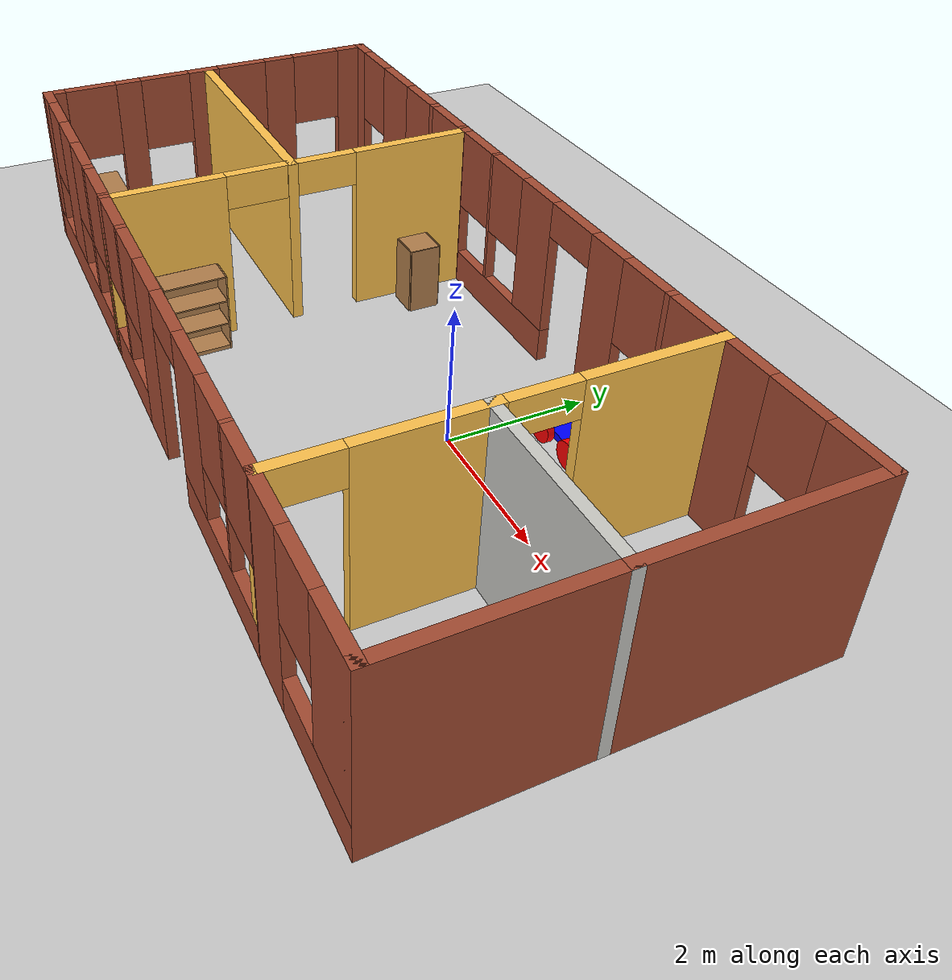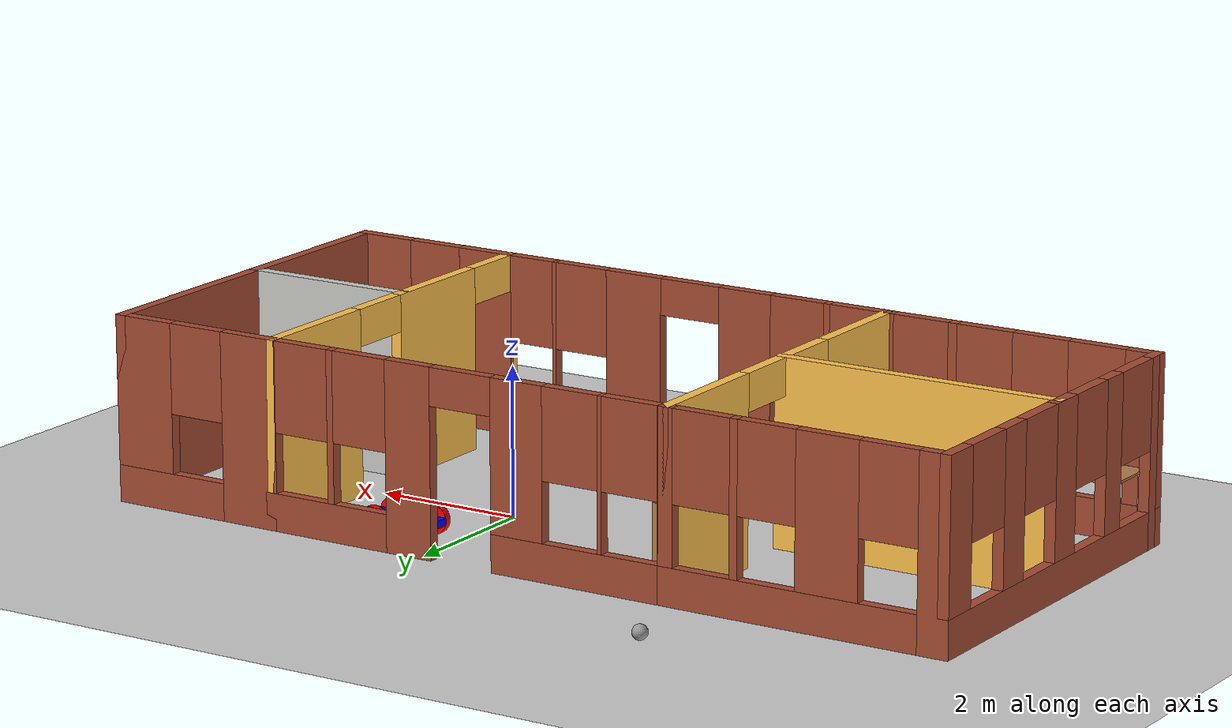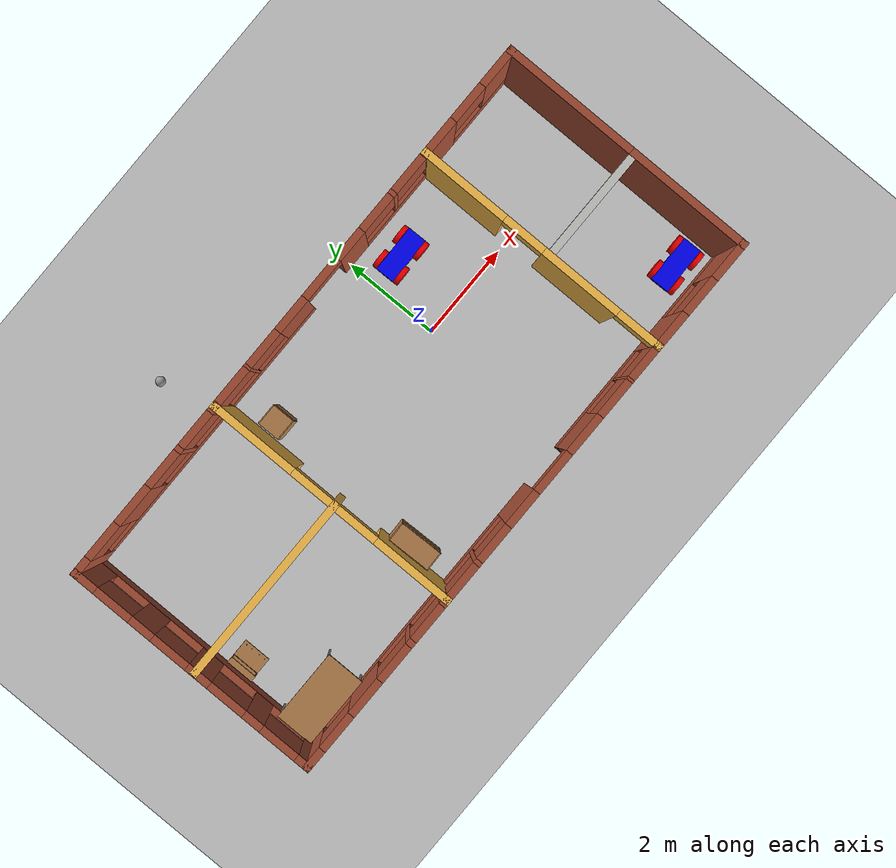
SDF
<sdf version="1.6">
 <world name="default">
  <plugin name="hello" filename="libhello.so"/>
  <light name="sun" type="directional">
   <pose>0 0 10 0 -0 0</pose>
   <diffuse>0.8 0.8 0.8 1</diffuse>
   <specular>0.2 0.2 0.2 1</specular>
   <attenuation>
    <range>1000</range>
    <constant>0.9</constant>
    <linear>0.01</linear>
    <quadratic>0.001</quadratic>
   </attenuation>
   <direction>-0.5 0.1 -0.9</direction>
  </light>
  <model name="ground_plane">
   <static>1</static>
   <link name="link">
    <collision name="collision">
     <geometry><plane><normal>0 0 1</normal><size>100 100</size></plane></geometry>
     <surface>
      <contact><collide_bitmask>65535</collide_bitmask></contact>
      <friction><ode><mu>100</mu><mu2>50</mu2></ode></friction>
     </surface>
    </collision>
    <visual name="visual">
     <cast_shadows>0</cast_shadows>
     <geometry><plane><normal>0 0 1</normal><size>100 100</size></plane></geometry>
     <material>
      <script><uri>file://media/materials/scripts/gazebo.material</uri><name>Gazebo/Grey</name></script>
     </material>
    </visual>
   </link>
  </model>
  <gravity>0 0 -9.8</gravity>
  <magnetic_field>6e-06 2.3e-05 -4.2e-05</magnetic_field>
  <atmosphere type="adiabatic"/>
  <physics name="default_physics" default="0" type="ode">
   <max_step_size>0.001</max_step_size>
   <real_time_factor>1</real_time_factor>
   <real_time_update_rate>1000</real_time_update_rate>
  </physics>
  <scene><ambient>0.4 0.4 0.4 1</ambient><background>0.7 0.7 0.7 1</background><shadows>1</shadows></scene>
  <spherical_coordinates>
   <surface_model>EARTH_WGS84</surface_model>
   <latitude_deg>0</latitude_deg>
   <longitude_deg>0</longitude_deg>
   <elevation>0</elevation>
   <heading_deg>0</heading_deg>
  </spherical_coordinates>
  <model name="building">
   <pose>-1.405 -0.625 0 0 -0 0</pose>
   <link name="Wall_0">
    <pose>-2.175 0 0 0 -0 1.5708</pose>
    <visual name="Wall_0_Visual_0">
     <pose>-1.89234 0 1.25 0 -0 0</pose>
     <geometry><box><size>1.71533 0.15 2.5</size></box></geometry>
     <material>
      <script><uri>file://media/materials/scripts/gazebo.material</uri><name>Gazebo/Grey</name></script>
      <ambient>1 0.764706 0.305882 1</ambient>
     </material>
     <meta><layer>0</layer></meta>
    </visual>
    <collision name="Wall_0_Collision_0">
     <geometry><box><size>1.71533 0.15 2.5</size></box></geometry>
     <pose>-1.89234 0 1.25 0 -0 0</pose>
    </collision>
    <visual name="Wall_0_Visual_1">
     <pose>-0.075798 0 1.25 0 -0 0</pose>
     <geometry><box><size>0.117747 0.15 2.5</size></box></geometry>
     <material>
      <script><uri>file://media/materials/scripts/gazebo.material</uri><name>Gazebo/Grey</name></script>
      <ambient>1 0.764706 0.305882 1</ambient>
     </material>
     <meta><layer>0</layer></meta>
    </visual>
    <collision name="Wall_0_Collision_1">
     <geometry><box><size>0.117747 0.15 2.5</size></box></geometry>
     <pose>-0.075798 0 1.25 0 -0 0</pose>
    </collision>
    <visual name="Wall_0_Visual_2">
     <pose>1.81654 0 1.25 0 -0 0</pose>
     <geometry><box><size>1.86692 0.15 2.5</size></box></geometry>
     <material>
      <script><uri>file://media/materials/scripts/gazebo.material</uri><name>Gazebo/Grey</name></script>
      <ambient>1 0.764706 0.305882 1</ambient>
     </material>
     <meta><layer>0</layer></meta>
    </visual>
    <collision name="Wall_0_Collision_2">
     <geometry><box><size>1.86692 0.15 2.5</size></box></geometry>
     <pose>1.81654 0 1.25 0 -0 0</pose>
    </collision>
    <visual name="Wall_0_Visual_3">
     <pose>-0.584671 0 2.25 0 -0 0</pose>
     <geometry><box><size>0.9 0.15 0.5</size></box></geometry>
     <material>
      <script><uri>file://media/materials/scripts/gazebo.material</uri><name>Gazebo/Grey</name></script>
      <ambient>1 0.764706 0.305882 1</ambient>
     </material>
     <meta><layer>0</layer></meta>
    </visual>
    <collision name="Wall_0_Collision_3">
     <geometry><box><size>0.9 0.15 0.5</size></box></geometry>
     <pose>-0.584671 0 2.25 0 -0 0</pose>
    </collision>
    <visual name="Wall_0_Visual_4">
     <pose>0.433076 0 2.25 0 -0 0</pose>
     <geometry><box><size>0.9 0.15 0.5</size></box></geometry>
     <material>
      <script><uri>file://media/materials/scripts/gazebo.material</uri><name>Gazebo/Grey</name></script>
      <ambient>1 0.764706 0.305882 1</ambient>
     </material>
     <meta><layer>0</layer></meta>
    </visual>
    <collision name="Wall_0_Collision_4">
     <geometry><box><size>0.9 0.15 0.5</size></box></geometry>
     <pose>0.433076 0 2.25 0 -0 0</pose>
    </collision>
   </link>
   <link name="Wall_1">
    <pose>0.75 2.675 0 0 -0 0</pose>
    <visual name="Wall_1_Visual_0">
     <pose>-2.92093 0 1.25 0 -0 0</pose>
     <geometry><box><size>0.158131 0.15 2.5</size></box></geometry>
     <material>
      <script><uri>file://media/materials/scripts/gazebo.material</uri><name>Gazebo/Bricks</name></script>
      <ambient>1 1 1 1</ambient>
     </material>
     <meta><layer>0</layer></meta>
    </visual>
    <collision name="Wall_1_Collision_0">
     <geometry><box><size>0.158131 0.15 2.5</size></box></geometry>
     <pose>-2.92093 0 1.25 0 -0 0</pose>
    </collision>
    <visual name="Wall_1_Visual_1">
     <pose>0.810048 0 1.25 0 -0 0</pose>
     <geometry><box><size>0.671635 0.15 2.5</size></box></geometry>
     <material>
      <script><uri>file://media/materials/scripts/gazebo.material</uri><name>Gazebo/Bricks</name></script>
      <ambient>1 1 1 1</ambient>
     </material>
     <meta><layer>0</layer></meta>
    </visual>
    <collision name="Wall_1_Collision_1">
     <geometry><box><size>0.671635 0.15 2.5</size></box></geometry>
     <pose>0.810048 0 1.25 0 -0 0</pose>
    </collision>
    <visual name="Wall_1_Visual_2">
     <pose>-1.63382 0 0.25 0 -0 0</pose>
     <geometry><box><size>2.4161 0.15 0.5</size></box></geometry>
     <material>
      <script><uri>file://media/materials/scripts/gazebo.material</uri><name>Gazebo/Bricks</name></script>
      <ambient>1 1 1 1</ambient>
     </material>
     <meta><layer>0</layer></meta>
    </visual>
    <collision name="Wall_1_Collision_2">
     <geometry><box><size>2.4161 0.15 0.5</size></box></geometry>
     <pose>-1.63382 0 0.25 0 -0 0</pose>
    </collision>
    <visual name="Wall_1_Visual_3">
     <pose>2.07293 0 0.25 0 -0 0</pose>
     <geometry><box><size>1.85413 0.15 0.5</size></box></geometry>
     <material>
      <script><uri>file://media/materials/scripts/gazebo.material</uri><name>Gazebo/Bricks</name></script>
      <ambient>1 1 1 1</ambient>
     </material>
     <meta><layer>0</layer></meta>
    </visual>
    <collision name="Wall_1_Collision_3">
     <geometry><box><size>1.85413 0.15 0.5</size></box></geometry>
     <pose>2.07293 0 0.25 0 -0 0</pose>
    </collision>
    <visual name="Wall_1_Visual_4">
     <pose>-2.01336 0 1.5 0 -0 0</pose>
     <geometry><box><size>0.057013 0.15 2</size></box></geometry>
     <material>
      <script><uri>file://media/materials/scripts/gazebo.material</uri><name>Gazebo/Bricks</name></script>
      <ambient>1 1 1 1</ambient>
     </material>
     <meta><layer>0</layer></meta>
    </visual>
    <collision name="Wall_1_Collision_4">
     <geometry><box><size>0.057013 0.15 2</size></box></geometry>
     <pose>-2.01336 0 1.5 0 -0 0</pose>
    </collision>
    <visual name="Wall_1_Visual_5">
     <pose>-0.805313 0 1.5 0 -0 0</pose>
     <geometry><box><size>0.759086 0.15 2</size></box></geometry>
     <material>
      <script><uri>file://media/materials/scripts/gazebo.material</uri><name>Gazebo/Bricks</name></script>
      <ambient>1 1 1 1</ambient>
     </material>
     <meta><layer>0</layer></meta>
    </visual>
    <collision name="Wall_1_Collision_5">
     <geometry><box><size>0.759086 0.15 2</size></box></geometry>
     <pose>-0.805313 0 1.5 0 -0 0</pose>
    </collision>
    <visual name="Wall_1_Visual_6">
     <pose>-0.805313 0 1.5 0 -0 0</pose>
     <geometry><box><size>0.759086 0.15 2</size></box></geometry>
     <material>
      <script><uri>file://media/materials/scripts/gazebo.material</uri><name>Gazebo/Bricks</name></script>
      <ambient>1 1 1 1</ambient>
     </material>
     <meta><layer>0</layer></meta>
    </visual>
    <collision name="Wall_1_Collision_6">
     <geometry><box><size>0.759086 0.15 2</size></box></geometry>
     <pose>-0.805313 0 1.5 0 -0 0</pose>
    </collision>
    <visual name="Wall_1_Visual_7">
     <pose>1.99186 0 1.5 0 -0 0</pose>
     <geometry><box><size>0.091993 0.15 2</size></box></geometry>
     <material>
      <script><uri>file://media/materials/scripts/gazebo.material</uri><name>Gazebo/Bricks</name></script>
      <ambient>1 1 1 1</ambient>
     </material>
     <meta><layer>0</layer></meta>
    </visual>
    <collision name="Wall_1_Collision_7">
     <geometry><box><size>0.091993 0.15 2</size></box></geometry>
     <pose>1.99186 0 1.5 0 -0 0</pose>
    </collision>
    <visual name="Wall_1_Visual_8">
     <pose>2.91893 0 1.5 0 -0 0</pose>
     <geometry><box><size>0.162141 0.15 2</size></box></geometry>
     <material>
      <script><uri>file://media/materials/scripts/gazebo.material</uri><name>Gazebo/Bricks</name></script>
      <ambient>1 1 1 1</ambient>
     </material>
     <meta><layer>0</layer></meta>
    </visual>
    <collision name="Wall_1_Collision_8">
     <geometry><box><size>0.162141 0.15 2</size></box></geometry>
     <pose>2.91893 0 1.5 0 -0 0</pose>
    </collision>
    <visual name="Wall_1_Visual_9">
     <pose>-2.44187 0 1.9 0 -0 0</pose>
     <geometry><box><size>0.8 0.15 1.2</size></box></geometry>
     <material>
      <script><uri>file://media/materials/scripts/gazebo.material</uri><name>Gazebo/Bricks</name></script>
      <ambient>1 1 1 1</ambient>
     </material>
     <meta><layer>0</layer></meta>
    </visual>
    <collision name="Wall_1_Collision_9">
     <geometry><box><size>0.8 0.15 1.2</size></box></geometry>
     <pose>-2.44187 0 1.9 0 -0 0</pose>
    </collision>
    <visual name="Wall_1_Visual_10">
     <pose>1.54587 0 1.9 0 -0 0</pose>
     <geometry><box><size>0.8 0.15 1.2</size></box></geometry>
     <material>
      <script><uri>file://media/materials/scripts/gazebo.material</uri><name>Gazebo/Bricks</name></script>
      <ambient>1 1 1 1</ambient>
     </material>
     <meta><layer>0</layer></meta>
    </visual>
    <collision name="Wall_1_Collision_10">
     <geometry><box><size>0.8 0.15 1.2</size></box></geometry>
     <pose>1.54587 0 1.9 0 -0 0</pose>
    </collision>
    <visual name="Wall_1_Visual_11">
     <pose>-1.58486 0 1.9 0 -0 0</pose>
     <geometry><box><size>0.8 0.15 1.2</size></box></geometry>
     <material>
      <script><uri>file://media/materials/scripts/gazebo.material</uri><name>Gazebo/Bricks</name></script>
      <ambient>1 1 1 1</ambient>
     </material>
     <meta><layer>0</layer></meta>
    </visual>
    <collision name="Wall_1_Collision_11">
     <geometry><box><size>0.8 0.15 1.2</size></box></geometry>
     <pose>-1.58486 0 1.9 0 -0 0</pose>
    </collision>
    <visual name="Wall_1_Visual_12">
     <pose>2.43786 0 1.9 0 -0 0</pose>
     <geometry><box><size>0.8 0.15 1.2</size></box></geometry>
     <material>
      <script><uri>file://media/materials/scripts/gazebo.material</uri><name>Gazebo/Bricks</name></script>
      <ambient>1 1 1 1</ambient>
     </material>
     <meta><layer>0</layer></meta>
    </visual>
    <collision name="Wall_1_Collision_12">
     <geometry><box><size>0.8 0.15 1.2</size></box></geometry>
     <pose>2.43786 0 1.9 0 -0 0</pose>
    </collision>
    <visual name="Wall_1_Visual_13">
     <pose>0.02423 0 2.25 0 -0 0</pose>
     <geometry><box><size>0.9 0.15 0.5</size></box></geometry>
     <material>
      <script><uri>file://media/materials/scripts/gazebo.material</uri><name>Gazebo/Bricks</name></script>
      <ambient>1 1 1 1</ambient>
     </material>
     <meta><layer>0</layer></meta>
    </visual>
    <collision name="Wall_1_Collision_13">
     <geometry><box><size>0.9 0.15 0.5</size></box></geometry>
     <pose>0.02423 0 2.25 0 -0 0</pose>
    </collision>
    <visual name="Wall_1_Visual_14">
     <pose>0.02423 0 2.25 0 -0 0</pose>
     <geometry><box><size>0.9 0.15 0.5</size></box></geometry>
     <material>
      <script><uri>file://media/materials/scripts/gazebo.material</uri><name>Gazebo/Bricks</name></script>
      <ambient>1 1 1 1</ambient>
     </material>
     <meta><layer>0</layer></meta>
    </visual>
    <collision name="Wall_1_Collision_14">
     <geometry><box><size>0.9 0.15 0.5</size></box></geometry>
     <pose>0.02423 0 2.25 0 -0 0</pose>
    </collision>
   </link>
   <link name="Wall_10">
    <collision name="Wall_10_Collision">
     <geometry><box><size>2.65 0.15 2.5</size></box></geometry>
     <pose>0 0 1.25 0 -0 0</pose>
    </collision>
    <visual name="Wall_10_Visual">
     <pose>0 0 1.25 0 -0 0</pose>
     <geometry><box><size>2.65 0.15 2.5</size></box></geometry>
     <material>
      <script><uri>file://media/materials/scripts/gazebo.material</uri><name>Gazebo/Bricks</name></script>
      <ambient>1 1 1 1</ambient>
     </material>
     <meta><layer>0</layer></meta>
    </visual>
    <pose>6.025 -1.425 0 0 -0 1.5708</pose>
   </link>
   <link name="Wall_12">
    <pose>-4.1 -2.675 0 0 -0 3.14159</pose>
    <visual name="Wall_12_Visual_0">
     <pose>-1.89685 0 1.25 0 -0 0</pose>
     <geometry><box><size>0.206292 0.15 2.5</size></box></geometry>
     <material>
      <script><uri>file://media/materials/scripts/gazebo.material</uri><name>Gazebo/Bricks</name></script>
      <ambient>1 1 1 1</ambient>
     </material>
     <meta><layer>0</layer></meta>
    </visual>
    <collision name="Wall_12_Collision_0">
     <geometry><box><size>0.206292 0.15 2.5</size></box></geometry>
     <pose>-1.89685 0 1.25 0 -0 0</pose>
    </collision>
    <visual name="Wall_12_Visual_1">
     <pose>0.103146 0 0.25 0 -0 0</pose>
     <geometry><box><size>3.79371 0.15 0.5</size></box></geometry>
     <material>
      <script><uri>file://media/materials/scripts/gazebo.material</uri><name>Gazebo/Bricks</name></script>
      <ambient>1 1 1 1</ambient>
     </material>
     <meta><layer>0</layer></meta>
    </visual>
    <collision name="Wall_12_Collision_1">
     <geometry><box><size>3.79371 0.15 0.5</size></box></geometry>
     <pose>0.103146 0 0.25 0 -0 0</pose>
    </collision>
    <visual name="Wall_12_Visual_2">
     <pose>-0.930221 0 1.5 0 -0 0</pose>
     <geometry><box><size>0.126973 0.15 2</size></box></geometry>
     <material>
      <script><uri>file://media/materials/scripts/gazebo.material</uri><name>Gazebo/Bricks</name></script>
      <ambient>1 1 1 1</ambient>
     </material>
     <meta><layer>0</layer></meta>
    </visual>
    <collision name="Wall_12_Collision_2">
     <geometry><box><size>0.126973 0.15 2</size></box></geometry>
     <pose>-0.930221 0 1.5 0 -0 0</pose>
    </collision>
    <visual name="Wall_12_Visual_3">
     <pose>0.329063 0 1.5 0 -0 0</pose>
     <geometry><box><size>0.791596 0.15 2</size></box></geometry>
     <material>
      <script><uri>file://media/materials/scripts/gazebo.material</uri><name>Gazebo/Bricks</name></script>
      <ambient>1 1 1 1</ambient>
     </material>
     <meta><layer>0</layer></meta>
    </visual>
    <collision name="Wall_12_Collision_3">
     <geometry><box><size>0.791596 0.15 2</size></box></geometry>
     <pose>0.329063 0 1.5 0 -0 0</pose>
    </collision>
    <visual name="Wall_12_Visual_4">
     <pose>1.76243 0 1.5 0 -0 0</pose>
     <geometry><box><size>0.475139 0.15 2</size></box></geometry>
     <material>
      <script><uri>file://media/materials/scripts/gazebo.material</uri><name>Gazebo/Bricks</name></script>
      <ambient>1 1 1 1</ambient>
     </material>
     <meta><layer>0</layer></meta>
    </visual>
    <collision name="Wall_12_Collision_4">
     <geometry><box><size>0.475139 0.15 2</size></box></geometry>
     <pose>1.76243 0 1.5 0 -0 0</pose>
    </collision>
    <visual name="Wall_12_Visual_5">
     <pose>-1.39371 0 1.9 0 -0 0</pose>
     <geometry><box><size>0.8 0.15 1.2</size></box></geometry>
     <material>
      <script><uri>file://media/materials/scripts/gazebo.material</uri><name>Gazebo/Bricks</name></script>
      <ambient>1 1 1 1</ambient>
     </material>
     <meta><layer>0</layer></meta>
    </visual>
    <collision name="Wall_12_Collision_5">
     <geometry><box><size>0.8 0.15 1.2</size></box></geometry>
     <pose>-1.39371 0 1.9 0 -0 0</pose>
    </collision>
    <visual name="Wall_12_Visual_6">
     <pose>-0.466734 0 1.9 0 -0 0</pose>
     <geometry><box><size>0.8 0.15 1.2</size></box></geometry>
     <material>
      <script><uri>file://media/materials/scripts/gazebo.material</uri><name>Gazebo/Bricks</name></script>
      <ambient>1 1 1 1</ambient>
     </material>
     <meta><layer>0</layer></meta>
    </visual>
    <collision name="Wall_12_Collision_6">
     <geometry><box><size>0.8 0.15 1.2</size></box></geometry>
     <pose>-0.466734 0 1.9 0 -0 0</pose>
    </collision>
    <visual name="Wall_12_Visual_7">
     <pose>1.12486 0 1.9 0 -0 0</pose>
     <geometry><box><size>0.8 0.15 1.2</size></box></geometry>
     <material>
      <script><uri>file://media/materials/scripts/gazebo.material</uri><name>Gazebo/Bricks</name></script>
      <ambient>1 1 1 1</ambient>
     </material>
     <meta><layer>0</layer></meta>
    </visual>
    <collision name="Wall_12_Collision_7">
     <geometry><box><size>0.8 0.15 1.2</size></box></geometry>
     <pose>1.12486 0 1.9 0 -0 0</pose>
    </collision>
   </link>
   <link name="Wall_13">
    <pose>-6.025 0 0 0 -0 1.5708</pose>
    <visual name="Wall_13_Visual_0">
     <pose>-2.58228 0 1.25 0 -0 0</pose>
     <geometry><box><size>0.335448 0.15 2.5</size></box></geometry>
     <material>
      <script><uri>file://media/materials/scripts/gazebo.material</uri><name>Gazebo/Bricks</name></script>
      <ambient>1 1 1 1</ambient>
     </material>
     <meta><layer>0</layer></meta>
    </visual>
    <collision name="Wall_13_Collision_0">
     <geometry><box><size>0.335448 0.15 2.5</size></box></geometry>
     <pose>-2.58228 0 1.25 0 -0 0</pose>
    </collision>
    <visual name="Wall_13_Visual_1">
     <pose>0.167724 0 0.25 0 -0 0</pose>
     <geometry><box><size>5.16455 0.15 0.5</size></box></geometry>
     <material>
      <script><uri>file://media/materials/scripts/gazebo.material</uri><name>Gazebo/Bricks</name></script>
      <ambient>1 1 1 1</ambient>
     </material>
     <meta><layer>0</layer></meta>
    </visual>
    <collision name="Wall_13_Collision_1">
     <geometry><box><size>5.16455 0.15 0.5</size></box></geometry>
     <pose>0.167724 0 0.25 0 -0 0</pose>
    </collision>
    <visual name="Wall_13_Visual_2">
     <pose>-1.41115 0 1.5 0 -0 0</pose>
     <geometry><box><size>0.406814 0.15 2</size></box></geometry>
     <material>
      <script><uri>file://media/materials/scripts/gazebo.material</uri><name>Gazebo/Bricks</name></script>
      <ambient>1 1 1 1</ambient>
     </material>
     <meta><layer>0</layer></meta>
    </visual>
    <collision name="Wall_13_Collision_2">
     <geometry><box><size>0.406814 0.15 2</size></box></geometry>
     <pose>-1.41115 0 1.5 0 -0 0</pose>
    </collision>
    <visual name="Wall_13_Visual_3">
     <pose>-0.15186 0 1.5 0 -0 0</pose>
     <geometry><box><size>0.511755 0.15 2</size></box></geometry>
     <material>
      <script><uri>file://media/materials/scripts/gazebo.material</uri><name>Gazebo/Bricks</name></script>
      <ambient>1 1 1 1</ambient>
     </material>
     <meta><layer>0</layer></meta>
    </visual>
    <collision name="Wall_13_Collision_3">
     <geometry><box><size>0.511755 0.15 2</size></box></geometry>
     <pose>-0.15186 0 1.5 0 -0 0</pose>
    </collision>
    <visual name="Wall_13_Visual_4">
     <pose>1.15989 0 1.5 0 -0 0</pose>
     <geometry><box><size>0.511755 0.15 2</size></box></geometry>
     <material>
      <script><uri>file://media/materials/scripts/gazebo.material</uri><name>Gazebo/Bricks</name></script>
      <ambient>1 1 1 1</ambient>
     </material>
     <meta><layer>0</layer></meta>
    </visual>
    <collision name="Wall_13_Collision_4">
     <geometry><box><size>0.511755 0.15 2</size></box></geometry>
     <pose>1.15989 0 1.5 0 -0 0</pose>
    </collision>
    <visual name="Wall_13_Visual_5">
     <pose>2.48289 0 1.5 0 -0 0</pose>
     <geometry><box><size>0.534228 0.15 2</size></box></geometry>
     <material>
      <script><uri>file://media/materials/scripts/gazebo.material</uri><name>Gazebo/Bricks</name></script>
      <ambient>1 1 1 1</ambient>
     </material>
     <meta><layer>0</layer></meta>
    </visual>
    <collision name="Wall_13_Collision_5">
     <geometry><box><size>0.534228 0.15 2</size></box></geometry>
     <pose>2.48289 0 1.5 0 -0 0</pose>
    </collision>
    <visual name="Wall_13_Visual_6">
     <pose>-2.01455 0 1.9 0 -0 0</pose>
     <geometry><box><size>0.8 0.15 1.2</size></box></geometry>
     <material>
      <script><uri>file://media/materials/scripts/gazebo.material</uri><name>Gazebo/Bricks</name></script>
      <ambient>1 1 1 1</ambient>
     </material>
     <meta><layer>0</layer></meta>
    </visual>
    <collision name="Wall_13_Collision_6">
     <geometry><box><size>0.8 0.15 1.2</size></box></geometry>
     <pose>-2.01455 0 1.9 0 -0 0</pose>
    </collision>
    <visual name="Wall_13_Visual_7">
     <pose>-0.807738 0 1.9 0 -0 0</pose>
     <geometry><box><size>0.8 0.15 1.2</size></box></geometry>
     <material>
      <script><uri>file://media/materials/scripts/gazebo.material</uri><name>Gazebo/Bricks</name></script>
      <ambient>1 1 1 1</ambient>
     </material>
     <meta><layer>0</layer></meta>
    </visual>
    <collision name="Wall_13_Collision_7">
     <geometry><box><size>0.8 0.15 1.2</size></box></geometry>
     <pose>-0.807738 0 1.9 0 -0 0</pose>
    </collision>
    <visual name="Wall_13_Visual_8">
     <pose>0.504017 0 1.9 0 -0 0</pose>
     <geometry><box><size>0.8 0.15 1.2</size></box></geometry>
     <material>
      <script><uri>file://media/materials/scripts/gazebo.material</uri><name>Gazebo/Bricks</name></script>
      <ambient>1 1 1 1</ambient>
     </material>
     <meta><layer>0</layer></meta>
    </visual>
    <collision name="Wall_13_Collision_8">
     <geometry><box><size>0.8 0.15 1.2</size></box></geometry>
     <pose>0.504017 0 1.9 0 -0 0</pose>
    </collision>
    <visual name="Wall_13_Visual_9">
     <pose>1.81577 0 1.9 0 -0 0</pose>
     <geometry><box><size>0.8 0.15 1.2</size></box></geometry>
     <material>
      <script><uri>file://media/materials/scripts/gazebo.material</uri><name>Gazebo/Bricks</name></script>
      <ambient>1 1 1 1</ambient>
     </material>
     <meta><layer>0</layer></meta>
    </visual>
    <collision name="Wall_13_Collision_9">
     <geometry><box><size>0.8 0.15 1.2</size></box></geometry>
     <pose>1.81577 0 1.9 0 -0 0</pose>
    </collision>
   </link>
   <link name="Wall_14">
    <pose>-4.1 2.675 0 0 -0 0</pose>
    <visual name="Wall_14_Visual_0">
     <pose>-1.78867 0 1.25 0 -0 0</pose>
     <geometry><box><size>0.422669 0.15 2.5</size></box></geometry>
     <material>
      <script><uri>file://media/materials/scripts/gazebo.material</uri><name>Gazebo/Bricks</name></script>
      <ambient>1 1 1 1</ambient>
     </material>
     <meta><layer>0</layer></meta>
    </visual>
    <collision name="Wall_14_Collision_0">
     <geometry><box><size>0.422669 0.15 2.5</size></box></geometry>
     <pose>-1.78867 0 1.25 0 -0 0</pose>
    </collision>
    <visual name="Wall_14_Visual_1">
     <pose>0.211334 0 0.25 0 -0 0</pose>
     <geometry><box><size>3.57733 0.15 0.5</size></box></geometry>
     <material>
      <script><uri>file://media/materials/scripts/gazebo.material</uri><name>Gazebo/Bricks</name></script>
      <ambient>1 1 1 1</ambient>
     </material>
     <meta><layer>0</layer></meta>
    </visual>
    <collision name="Wall_14_Collision_1">
     <geometry><box><size>3.57733 0.15 0.5</size></box></geometry>
     <pose>0.211334 0 0.25 0 -0 0</pose>
    </collision>
    <visual name="Wall_14_Visual_2">
     <pose>-0.346553 0 1.5 0 -0 0</pose>
     <geometry><box><size>0.861556 0.15 2</size></box></geometry>
     <material>
      <script><uri>file://media/materials/scripts/gazebo.material</uri><name>Gazebo/Bricks</name></script>
      <ambient>1 1 1 1</ambient>
     </material>
     <meta><layer>0</layer></meta>
    </visual>
    <collision name="Wall_14_Collision_2">
     <geometry><box><size>0.861556 0.15 2</size></box></geometry>
     <pose>-0.346553 0 1.5 0 -0 0</pose>
    </collision>
    <visual name="Wall_14_Visual_3">
     <pose>0.938966 0 1.5 0 -0 0</pose>
     <geometry><box><size>0.109483 0.15 2</size></box></geometry>
     <material>
      <script><uri>file://media/materials/scripts/gazebo.material</uri><name>Gazebo/Bricks</name></script>
      <ambient>1 1 1 1</ambient>
     </material>
     <meta><layer>0</layer></meta>
    </visual>
    <collision name="Wall_14_Collision_3">
     <geometry><box><size>0.109483 0.15 2</size></box></geometry>
     <pose>0.938966 0 1.5 0 -0 0</pose>
    </collision>
    <visual name="Wall_14_Visual_4">
     <pose>1.89685 0 1.5 0 -0 0</pose>
     <geometry><box><size>0.206292 0.15 2</size></box></geometry>
     <material>
      <script><uri>file://media/materials/scripts/gazebo.material</uri><name>Gazebo/Bricks</name></script>
      <ambient>1 1 1 1</ambient>
     </material>
     <meta><layer>0</layer></meta>
    </visual>
    <collision name="Wall_14_Collision_4">
     <geometry><box><size>0.206292 0.15 2</size></box></geometry>
     <pose>1.89685 0 1.5 0 -0 0</pose>
    </collision>
    <visual name="Wall_14_Visual_5">
     <pose>-1.17733 0 1.9 0 -0 0</pose>
     <geometry><box><size>0.8 0.15 1.2</size></box></geometry>
     <material>
      <script><uri>file://media/materials/scripts/gazebo.material</uri><name>Gazebo/Bricks</name></script>
      <ambient>1 1 1 1</ambient>
     </material>
     <meta><layer>0</layer></meta>
    </visual>
    <collision name="Wall_14_Collision_5">
     <geometry><box><size>0.8 0.15 1.2</size></box></geometry>
     <pose>-1.17733 0 1.9 0 -0 0</pose>
    </collision>
    <visual name="Wall_14_Visual_6">
     <pose>0.484225 0 1.9 0 -0 0</pose>
     <geometry><box><size>0.8 0.15 1.2</size></box></geometry>
     <material>
      <script><uri>file://media/materials/scripts/gazebo.material</uri><name>Gazebo/Bricks</name></script>
      <ambient>1 1 1 1</ambient>
     </material>
     <meta><layer>0</layer></meta>
    </visual>
    <collision name="Wall_14_Collision_6">
     <geometry><box><size>0.8 0.15 1.2</size></box></geometry>
     <pose>0.484225 0 1.9 0 -0 0</pose>
    </collision>
    <visual name="Wall_14_Visual_7">
     <pose>1.39371 0 1.9 0 -0 0</pose>
     <geometry><box><size>0.8 0.15 1.2</size></box></geometry>
     <material>
      <script><uri>file://media/materials/scripts/gazebo.material</uri><name>Gazebo/Bricks</name></script>
      <ambient>1 1 1 1</ambient>
     </material>
     <meta><layer>0</layer></meta>
    </visual>
    <collision name="Wall_14_Collision_7">
     <geometry><box><size>0.8 0.15 1.2</size></box></geometry>
     <pose>1.39371 0 1.9 0 -0 0</pose>
    </collision>
   </link>
   <link name="Wall_17">
    <collision name="Wall_17_Collision">
     <geometry><box><size>4 0.15 2.5</size></box></geometry>
     <pose>0 0 1.25 0 -0 0</pose>
    </collision>
    <visual name="Wall_17_Visual">
     <pose>0 0 1.25 0 -0 0</pose>
     <geometry><box><size>4 0.15 2.5</size></box></geometry>
     <material>
      <script><uri>file://media/materials/scripts/gazebo.material</uri><name>Gazebo/Grey</name></script>
      <ambient>1 0.764706 0.305882 1</ambient>
     </material>
     <meta><layer>0</layer></meta>
    </visual>
    <pose>-4.08598 -0.075797 0 0 -0 0</pose>
   </link>
   <link name="Wall_2">
    <pose>3.675 0 0 0 0 -1.5708</pose>
    <visual name="Wall_2_Visual_0">
     <pose>-1.80497 0 1.25 0 -0 0</pose>
     <geometry><box><size>1.89006 0.15 2.5</size></box></geometry>
     <material>
      <script><uri>file://media/materials/scripts/gazebo.material</uri><name>Gazebo/Grey</name></script>
      <ambient>1 0.764706 0.305882 1</ambient>
     </material>
     <meta><layer>0</layer></meta>
    </visual>
    <collision name="Wall_2_Collision_0">
     <geometry><box><size>1.89006 0.15 2.5</size></box></geometry>
     <pose>-1.80497 0 1.25 0 -0 0</pose>
    </collision>
    <visual name="Wall_2_Visual_1">
     <pose>0.896934 0 1.25 0 -0 0</pose>
     <geometry><box><size>1.71376 0.15 2.5</size></box></geometry>
     <material>
      <script><uri>file://media/materials/scripts/gazebo.material</uri><name>Gazebo/Grey</name></script>
      <ambient>1 0.764706 0.305882 1</ambient>
     </material>
     <meta><layer>0</layer></meta>
    </visual>
    <collision name="Wall_2_Collision_1">
     <geometry><box><size>1.71376 0.15 2.5</size></box></geometry>
     <pose>0.896934 0 1.25 0 -0 0</pose>
    </collision>
    <visual name="Wall_2_Visual_2">
     <pose>2.70191 0 1.25 0 -0 0</pose>
     <geometry><box><size>0.096187 0.15 2.5</size></box></geometry>
     <material>
      <script><uri>file://media/materials/scripts/gazebo.material</uri><name>Gazebo/Grey</name></script>
      <ambient>1 0.764706 0.305882 1</ambient>
     </material>
     <meta><layer>0</layer></meta>
    </visual>
    <collision name="Wall_2_Collision_2">
     <geometry><box><size>0.096187 0.15 2.5</size></box></geometry>
     <pose>2.70191 0 1.25 0 -0 0</pose>
    </collision>
    <visual name="Wall_2_Visual_3">
     <pose>-0.409945 0 2.25 0 -0 0</pose>
     <geometry><box><size>0.9 0.15 0.5</size></box></geometry>
     <material>
      <script><uri>file://media/materials/scripts/gazebo.material</uri><name>Gazebo/Grey</name></script>
      <ambient>1 0.764706 0.305882 1</ambient>
     </material>
     <meta><layer>0</layer></meta>
    </visual>
    <collision name="Wall_2_Collision_3">
     <geometry><box><size>0.9 0.15 0.5</size></box></geometry>
     <pose>-0.409945 0 2.25 0 -0 0</pose>
    </collision>
    <visual name="Wall_2_Visual_4">
     <pose>2.20381 0 2.25 0 -0 0</pose>
     <geometry><box><size>0.9 0.15 0.5</size></box></geometry>
     <material>
      <script><uri>file://media/materials/scripts/gazebo.material</uri><name>Gazebo/Grey</name></script>
      <ambient>1 0.764706 0.305882 1</ambient>
     </material>
     <meta><layer>0</layer></meta>
    </visual>
    <collision name="Wall_2_Collision_4">
     <geometry><box><size>0.9 0.15 0.5</size></box></geometry>
     <pose>2.20381 0 2.25 0 -0 0</pose>
    </collision>
   </link>
   <link name="Wall_3">
    <pose>0.75 -2.675 0 0 -0 3.14159</pose>
    <visual name="Wall_3_Visual_0">
     <pose>-2.98889 0 1.25 0 -0 0</pose>
     <geometry><box><size>0.022221 0.15 2.5</size></box></geometry>
     <material>
      <script><uri>file://media/materials/scripts/gazebo.material</uri><name>Gazebo/Bricks</name></script>
      <ambient>1 0.764706 0.305882 1</ambient>
     </material>
     <meta><layer>0</layer></meta>
    </visual>
    <collision name="Wall_3_Collision_0">
     <geometry><box><size>0.022221 0.15 2.5</size></box></geometry>
     <pose>-2.98889 0 1.25 0 -0 0</pose>
    </collision>
    <visual name="Wall_3_Visual_1">
     <pose>0.826774 0 1.25 0 -0 0</pose>
     <geometry><box><size>0.786123 0.15 2.5</size></box></geometry>
     <material>
      <script><uri>file://media/materials/scripts/gazebo.material</uri><name>Gazebo/Bricks</name></script>
      <ambient>1 0.764706 0.305882 1</ambient>
     </material>
     <meta><layer>0</layer></meta>
    </visual>
    <collision name="Wall_3_Collision_1">
     <geometry><box><size>0.786123 0.15 2.5</size></box></geometry>
     <pose>0.826774 0 1.25 0 -0 0</pose>
    </collision>
    <visual name="Wall_3_Visual_2">
     <pose>-1.72203 0 0.25 0 -0 0</pose>
     <geometry><box><size>2.51149 0.15 0.5</size></box></geometry>
     <material>
      <script><uri>file://media/materials/scripts/gazebo.material</uri><name>Gazebo/Bricks</name></script>
      <ambient>1 0.764706 0.305882 1</ambient>
     </material>
     <meta><layer>0</layer></meta>
    </visual>
    <collision name="Wall_3_Collision_2">
     <geometry><box><size>2.51149 0.15 0.5</size></box></geometry>
     <pose>-1.72203 0 0.25 0 -0 0</pose>
    </collision>
    <visual name="Wall_3_Visual_3">
     <pose>2.10992 0 0.25 0 -0 0</pose>
     <geometry><box><size>1.78016 0.15 0.5</size></box></geometry>
     <material>
      <script><uri>file://media/materials/scripts/gazebo.material</uri><name>Gazebo/Bricks</name></script>
      <ambient>1 0.764706 0.305882 1</ambient>
     </material>
     <meta><layer>0</layer></meta>
    </visual>
    <collision name="Wall_3_Collision_3">
     <geometry><box><size>1.78016 0.15 0.5</size></box></geometry>
     <pose>2.10992 0 0.25 0 -0 0</pose>
    </collision>
    <visual name="Wall_3_Visual_4">
     <pose>-2.14927 0 1.5 0 -0 0</pose>
     <geometry><box><size>0.057013 0.15 2</size></box></geometry>
     <material>
      <script><uri>file://media/materials/scripts/gazebo.material</uri><name>Gazebo/Bricks</name></script>
      <ambient>1 0.764706 0.305882 1</ambient>
     </material>
     <meta><layer>0</layer></meta>
    </visual>
    <collision name="Wall_3_Collision_4">
     <geometry><box><size>0.057013 0.15 2</size></box></geometry>
     <pose>-2.14927 0 1.5 0 -0 0</pose>
    </collision>
    <visual name="Wall_3_Visual_5">
     <pose>-0.893527 0 1.5 0 -0 0</pose>
     <geometry><box><size>0.854479 0.15 2</size></box></geometry>
     <material>
      <script><uri>file://media/materials/scripts/gazebo.material</uri><name>Gazebo/Bricks</name></script>
      <ambient>1 0.764706 0.305882 1</ambient>
     </material>
     <meta><layer>0</layer></meta>
    </visual>
    <collision name="Wall_3_Collision_5">
     <geometry><box><size>0.854479 0.15 2</size></box></geometry>
     <pose>-0.893527 0 1.5 0 -0 0</pose>
    </collision>
    <visual name="Wall_3_Visual_6">
     <pose>-0.893527 0 1.5 0 -0 0</pose>
     <geometry><box><size>0.854479 0.15 2</size></box></geometry>
     <material>
      <script><uri>file://media/materials/scripts/gazebo.material</uri><name>Gazebo/Bricks</name></script>
      <ambient>1 0.764706 0.305882 1</ambient>
     </material>
     <meta><layer>0</layer></meta>
    </visual>
    <collision name="Wall_3_Collision_6">
     <geometry><box><size>0.854479 0.15 2</size></box></geometry>
     <pose>-0.893527 0 1.5 0 -0 0</pose>
    </collision>
    <visual name="Wall_3_Visual_7">
     <pose>2.06583 0 1.5 0 -0 0</pose>
     <geometry><box><size>0.091993 0.15 2</size></box></geometry>
     <material>
      <script><uri>file://media/materials/scripts/gazebo.material</uri><name>Gazebo/Bricks</name></script>
      <ambient>1 0.764706 0.305882 1</ambient>
     </material>
     <meta><layer>0</layer></meta>
    </visual>
    <collision name="Wall_3_Collision_7">
     <geometry><box><size>0.091993 0.15 2</size></box></geometry>
     <pose>2.06583 0 1.5 0 -0 0</pose>
    </collision>
    <visual name="Wall_3_Visual_8">
     <pose>2.95591 0 1.5 0 -0 0</pose>
     <geometry><box><size>0.088171 0.15 2</size></box></geometry>
     <material>
      <script><uri>file://media/materials/scripts/gazebo.material</uri><name>Gazebo/Bricks</name></script>
      <ambient>1 0.764706 0.305882 1</ambient>
     </material>
     <meta><layer>0</layer></meta>
    </visual>
    <collision name="Wall_3_Collision_8">
     <geometry><box><size>0.088171 0.15 2</size></box></geometry>
     <pose>2.95591 0 1.5 0 -0 0</pose>
    </collision>
    <visual name="Wall_3_Visual_9">
     <pose>-2.57778 0 1.9 0 -0 0</pose>
     <geometry><box><size>0.8 0.15 1.2</size></box></geometry>
     <material>
      <script><uri>file://media/materials/scripts/gazebo.material</uri><name>Gazebo/Bricks</name></script>
      <ambient>1 0.764706 0.305882 1</ambient>
     </material>
     <meta><layer>0</layer></meta>
    </visual>
    <collision name="Wall_3_Collision_9">
     <geometry><box><size>0.8 0.15 1.2</size></box></geometry>
     <pose>-2.57778 0 1.9 0 -0 0</pose>
    </collision>
    <visual name="Wall_3_Visual_10">
     <pose>1.61984 0 1.9 0 -0 0</pose>
     <geometry><box><size>0.8 0.15 1.2</size></box></geometry>
     <material>
      <script><uri>file://media/materials/scripts/gazebo.material</uri><name>Gazebo/Bricks</name></script>
      <ambient>1 0.764706 0.305882 1</ambient>
     </material>
     <meta><layer>0</layer></meta>
    </visual>
    <collision name="Wall_3_Collision_10">
     <geometry><box><size>0.8 0.15 1.2</size></box></geometry>
     <pose>1.61984 0 1.9 0 -0 0</pose>
    </collision>
    <visual name="Wall_3_Visual_11">
     <pose>-1.72077 0 1.9 0 -0 0</pose>
     <geometry><box><size>0.8 0.15 1.2</size></box></geometry>
     <material>
      <script><uri>file://media/materials/scripts/gazebo.material</uri><name>Gazebo/Bricks</name></script>
      <ambient>1 0.764706 0.305882 1</ambient>
     </material>
     <meta><layer>0</layer></meta>
    </visual>
    <collision name="Wall_3_Collision_11">
     <geometry><box><size>0.8 0.15 1.2</size></box></geometry>
     <pose>-1.72077 0 1.9 0 -0 0</pose>
    </collision>
    <visual name="Wall_3_Visual_12">
     <pose>2.51183 0 1.9 0 -0 0</pose>
     <geometry><box><size>0.8 0.15 1.2</size></box></geometry>
     <material>
      <script><uri>file://media/materials/scripts/gazebo.material</uri><name>Gazebo/Bricks</name></script>
      <ambient>1 0.764706 0.305882 1</ambient>
     </material>
     <meta><layer>0</layer></meta>
    </visual>
    <collision name="Wall_3_Collision_12">
     <geometry><box><size>0.8 0.15 1.2</size></box></geometry>
     <pose>2.51183 0 1.9 0 -0 0</pose>
    </collision>
    <visual name="Wall_3_Visual_13">
     <pose>-0.016287 0 2.25 0 -0 0</pose>
     <geometry><box><size>0.9 0.15 0.5</size></box></geometry>
     <material>
      <script><uri>file://media/materials/scripts/gazebo.material</uri><name>Gazebo/Bricks</name></script>
      <ambient>1 0.764706 0.305882 1</ambient>
     </material>
     <meta><layer>0</layer></meta>
    </visual>
    <collision name="Wall_3_Collision_13">
     <geometry><box><size>0.9 0.15 0.5</size></box></geometry>
     <pose>-0.016287 0 2.25 0 -0 0</pose>
    </collision>
    <visual name="Wall_3_Visual_14">
     <pose>-0.016287 0 2.25 0 -0 0</pose>
     <geometry><box><size>0.9 0.15 0.5</size></box></geometry>
     <material>
      <script><uri>file://media/materials/scripts/gazebo.material</uri><name>Gazebo/Bricks</name></script>
      <ambient>1 0.764706 0.305882 1</ambient>
     </material>
     <meta><layer>0</layer></meta>
    </visual>
    <collision name="Wall_3_Collision_14">
     <geometry><box><size>0.9 0.15 0.5</size></box></geometry>
     <pose>-0.016287 0 2.25 0 -0 0</pose>
    </collision>
   </link>
   <link name="Wall_5">
    <pose>4.85 2.675 0 0 -0 0</pose>
    <visual name="Wall_5_Visual_0">
     <pose>-0.834038 0 1.25 0 -0 0</pose>
     <geometry><box><size>0.831925 0.15 2.5</size></box></geometry>
     <material>
      <script><uri>file://media/materials/scripts/gazebo.material</uri><name>Gazebo/Bricks</name></script>
      <ambient>1 1 1 1</ambient>
     </material>
     <meta><layer>0</layer></meta>
    </visual>
    <collision name="Wall_5_Collision_0">
     <geometry><box><size>0.831925 0.15 2.5</size></box></geometry>
     <pose>-0.834038 0 1.25 0 -0 0</pose>
    </collision>
    <visual name="Wall_5_Visual_1">
     <pose>0.415962 0 0.25 0 -0 0</pose>
     <geometry><box><size>1.66807 0.15 0.5</size></box></geometry>
     <material>
      <script><uri>file://media/materials/scripts/gazebo.material</uri><name>Gazebo/Bricks</name></script>
      <ambient>1 1 1 1</ambient>
     </material>
     <meta><layer>0</layer></meta>
    </visual>
    <collision name="Wall_5_Collision_1">
     <geometry><box><size>1.66807 0.15 0.5</size></box></geometry>
     <pose>0.415962 0 0.25 0 -0 0</pose>
    </collision>
    <visual name="Wall_5_Visual_2">
     <pose>0.815962 0 1.5 0 -0 0</pose>
     <geometry><box><size>0.868075 0.15 2</size></box></geometry>
     <material>
      <script><uri>file://media/materials/scripts/gazebo.material</uri><name>Gazebo/Bricks</name></script>
      <ambient>1 1 1 1</ambient>
     </material>
     <meta><layer>0</layer></meta>
    </visual>
    <collision name="Wall_5_Collision_2">
     <geometry><box><size>0.868075 0.15 2</size></box></geometry>
     <pose>0.815962 0 1.5 0 -0 0</pose>
    </collision>
    <visual name="Wall_5_Visual_3">
     <pose>-0.018075 0 1.9 0 -0 0</pose>
     <geometry><box><size>0.8 0.15 1.2</size></box></geometry>
     <material>
      <script><uri>file://media/materials/scripts/gazebo.material</uri><name>Gazebo/Bricks</name></script>
      <ambient>1 1 1 1</ambient>
     </material>
     <meta><layer>0</layer></meta>
    </visual>
    <collision name="Wall_5_Collision_3">
     <geometry><box><size>0.8 0.15 1.2</size></box></geometry>
     <pose>-0.018075 0 1.9 0 -0 0</pose>
    </collision>
   </link>
   <link name="Wall_6">
    <collision name="Wall_6_Collision">
     <geometry><box><size>3 0.15 2.5</size></box></geometry>
     <pose>0 0 1.25 0 -0 0</pose>
    </collision>
    <visual name="Wall_6_Visual">
     <pose>0 0 1.25 0 -0 0</pose>
     <geometry><box><size>3 0.15 2.5</size></box></geometry>
     <material>
      <script><uri>file://media/materials/scripts/gazebo.material</uri><name>Gazebo/Bricks</name></script>
      <ambient>1 1 1 1</ambient>
     </material>
     <meta><layer>0</layer></meta>
    </visual>
    <pose>6.025 1.25 0 0 0 -1.5708</pose>
   </link>
   <link name="Wall_7">
    <collision name="Wall_7_Collision">
     <geometry><box><size>2.5 0.15 2.5</size></box></geometry>
     <pose>0 0 1.25 0 -0 0</pose>
    </collision>
    <visual name="Wall_7_Visual">
     <pose>0 0 1.25 0 -0 0</pose>
     <geometry><box><size>2.5 0.15 2.5</size></box></geometry>
     <material>
      <script><uri>file://media/materials/scripts/gazebo.material</uri><name>Gazebo/CeilingTiled</name></script>
      <ambient>1 0.764706 0.305882 1</ambient>
     </material>
     <meta><layer>0</layer></meta>
    </visual>
    <pose>4.85 -0.175 0 0 -0 3.14159</pose>
   </link>
   <link name="Wall_9">
    <pose>4.85 -2.675 0 0 -0 0</pose>
    <visual name="Wall_9_Visual_0">
     <pose>-0.834038 0 1.25 0 -0 0</pose>
     <geometry><box><size>0.831925 0.15 2.5</size></box></geometry>
     <material>
      <script><uri>file://media/materials/scripts/gazebo.material</uri><name>Gazebo/Bricks</name></script>
      <ambient>1 1 1 1</ambient>
     </material>
     <meta><layer>0</layer></meta>
    </visual>
    <collision name="Wall_9_Collision_0">
     <geometry><box><size>0.831925 0.15 2.5</size></box></geometry>
     <pose>-0.834038 0 1.25 0 -0 0</pose>
    </collision>
    <visual name="Wall_9_Visual_1">
     <pose>0.415962 0 0.25 0 -0 0</pose>
     <geometry><box><size>1.66807 0.15 0.5</size></box></geometry>
     <material>
      <script><uri>file://media/materials/scripts/gazebo.material</uri><name>Gazebo/Bricks</name></script>
      <ambient>1 1 1 1</ambient>
     </material>
     <meta><layer>0</layer></meta>
    </visual>
    <collision name="Wall_9_Collision_1">
     <geometry><box><size>1.66807 0.15 0.5</size></box></geometry>
     <pose>0.415962 0 0.25 0 -0 0</pose>
    </collision>
    <visual name="Wall_9_Visual_2">
     <pose>0.815962 0 1.5 0 -0 0</pose>
     <geometry><box><size>0.868075 0.15 2</size></box></geometry>
     <material>
      <script><uri>file://media/materials/scripts/gazebo.material</uri><name>Gazebo/Bricks</name></script>
      <ambient>1 1 1 1</ambient>
     </material>
     <meta><layer>0</layer></meta>
    </visual>
    <collision name="Wall_9_Collision_2">
     <geometry><box><size>0.868075 0.15 2</size></box></geometry>
     <pose>0.815962 0 1.5 0 -0 0</pose>
    </collision>
    <visual name="Wall_9_Visual_3">
     <pose>-0.018075 0 1.9 0 -0 0</pose>
     <geometry><box><size>0.8 0.15 1.2</size></box></geometry>
     <material>
      <script><uri>file://media/materials/scripts/gazebo.material</uri><name>Gazebo/Bricks</name></script>
      <ambient>1 1 1 1</ambient>
     </material>
     <meta><layer>0</layer></meta>
    </visual>
    <collision name="Wall_9_Collision_3">
     <geometry><box><size>0.8 0.15 1.2</size></box></geometry>
     <pose>-0.018075 0 1.9 0 -0 0</pose>
    </collision>
   </link>
   <static>1</static>
  </model>
  <model name="cabinet">
   <static>1</static>
   <link name="cabinet_bottom_plate">
    <inertial>
     <pose>0 0 -1 0 -0 0</pose>
     <inertia><ixx>2.05</ixx><ixy>0</ixy><ixz>0</ixz><iyy>2.05</iyy><iyz>0</iyz><izz>2.05</izz></inertia>
     <mass>25</mass>
    </inertial>
    <collision name="cabinet_bottom_plate_geom">
     <pose>0 0 0.01 0 -0 0</pose>
     <geometry><box><size>0.45 0.45 0.02</size></box></geometry>
    </collision>
    <visual name="cabinet_bottom_plate_geom_visual">
     <pose>0 0 0.01 0 -0 0</pose>
     <geometry><box><size>0.45 0.45 0.02</size></box></geometry>
     <material>
      <script><uri>file://media/materials/scripts/gazebo.material</uri><name>Gazebo/Wood</name></script>
     </material>
    </visual>
    <collision name="cabinet_bottom_plate_geom_cabinet_back_plate">
     <pose>0.235 0 0.51 0 -0 0</pose>
     <geometry><box><size>0.02 0.45 1.02</size></box></geometry>
    </collision>
    <visual name="cabinet_bottom_plate_geom_cabinet_back_plate_visual">
     <pose>0.235 0 0.51 0 -0 0</pose>
     <geometry><box><size>0.02 0.45 1.02</size></box></geometry>
     <material>
      <script><uri>file://media/materials/scripts/gazebo.material</uri><name>Gazebo/Wood</name></script>
     </material>
    </visual>
    <collision name="cabinet_bottom_plate_geom_cabinet_left_plate">
     <pose>0 0.235 0.51 0 -0 0</pose>
     <geometry><box><size>0.45 0.02 1.02</size></box></geometry>
    </collision>
    <visual name="cabinet_bottom_plate_geom_cabinet_left_plate_visual">
     <pose>0 0.235 0.51 0 -0 0</pose>
     <geometry><box><size>0.45 0.02 1.02</size></box></geometry>
     <material>
      <script><uri>file://media/materials/scripts/gazebo.material</uri><name>Gazebo/Wood</name></script>
     </material>
    </visual>
    <collision name="cabinet_bottom_plate_geom_cabinet_middle_plate">
     <pose>0 0 0.51 0 -0 0</pose>
     <geometry><box><size>0.45 0.45 0.02</size></box></geometry>
    </collision>
    <visual name="cabinet_bottom_plate_geom_cabinet_middle_plate_visual">
     <pose>0 0 0.51 0 -0 0</pose>
     <geometry><box><size>0.45 0.45 0.02</size></box></geometry>
     <material>
      <script><uri>file://media/materials/scripts/gazebo.material</uri><name>Gazebo/Wood</name></script>
     </material>
    </visual>
    <collision name="cabinet_bottom_plate_geom_cabinet_right_plate">
     <pose>0 -0.235 0.51 0 -0 0</pose>
     <geometry><box><size>0.45 0.02 1.02</size></box></geometry>
    </collision>
    <visual name="cabinet_bottom_plate_geom_cabinet_right_plate_visual">
     <pose>0 -0.235 0.51 0 -0 0</pose>
     <geometry><box><size>0.45 0.02 1.02</size></box></geometry>
     <material>
      <script><uri>file://media/materials/scripts/gazebo.material</uri><name>Gazebo/Wood</name></script>
     </material>
    </visual>
    <collision name="cabinet_bottom_plate_geom_cabinet_top_plate">
     <pose>0 0 1.01 0 -0 0</pose>
     <geometry><box><size>0.45 0.45 0.02</size></box></geometry>
    </collision>
    <visual name="cabinet_bottom_plate_geom_cabinet_top_plate_visual">
     <pose>0 0 1.01 0 -0 0</pose>
     <geometry><box><size>0.45 0.45 0.02</size></box></geometry>
     <material>
      <script><uri>file://media/materials/scripts/gazebo.material</uri><name>Gazebo/Wood</name></script>
     </material>
    </visual>
   </link>
   <pose>-3.18497 1.12425 0 0 -0 0</pose>
  </model>
  <model name="bookshelf">
   <static>1</static>
   <link name="link">
    <inertial><mass>1</mass></inertial>
    <collision name="back">
     <pose>0 0.005 0.6 0 -0 0</pose>
     <geometry><box><size>0.9 0.01 1.2</size></box></geometry>
    </collision>
    <visual name="visual1">
     <pose>0 0.005 0.6 0 -0 0</pose>
     <geometry><box><size>0.9 0.01 1.2</size></box></geometry>
     <material>
      <script><uri>file://media/materials/scripts/gazebo.material</uri><name>Gazebo/Wood</name></script>
     </material>
    </visual>
    <collision name="left_side">
     <pose>0.45 -0.195 0.6 0 -0 0</pose>
     <geometry><box><size>0.02 0.4 1.2</size></box></geometry>
    </collision>
    <visual name="visual2">
     <pose>0.45 -0.195 0.6 0 -0 0</pose>
     <geometry><box><size>0.02 0.4 1.2</size></box></geometry>
     <material>
      <script><uri>file://media/materials/scripts/gazebo.material</uri><name>Gazebo/Wood</name></script>
     </material>
    </visual>
    <collision name="right_side">
     <pose>-0.45 -0.195 0.6 0 -0 0</pose>
     <geometry><box><size>0.02 0.4 1.2</size></box></geometry>
    </collision>
    <visual name="visual3">
     <pose>-0.45 -0.195 0.6 0 -0 0</pose>
     <geometry><box><size>0.02 0.4 1.2</size></box></geometry>
     <material>
      <script><uri>file://media/materials/scripts/gazebo.material</uri><name>Gazebo/Wood</name></script>
     </material>
    </visual>
    <collision name="bottom">
     <pose>0 -0.195 0.03 0 -0 0</pose>
     <geometry><box><size>0.88 0.4 0.06</size></box></geometry>
    </collision>
    <visual name="visual4">
     <pose>0 -0.195 0.03 0 -0 0</pose>
     <geometry><box><size>0.88 0.4 0.06</size></box></geometry>
     <material>
      <script><uri>file://media/materials/scripts/gazebo.material</uri><name>Gazebo/Wood</name></script>
     </material>
    </visual>
    <collision name="top">
     <pose>0 -0.195 1.19 0 -0 0</pose>
     <geometry><box><size>0.88 0.4 0.02</size></box></geometry>
    </collision>
    <visual name="visual5">
     <pose>0 -0.195 1.19 0 -0 0</pose>
     <geometry><box><size>0.88 0.4 0.02</size></box></geometry>
     <material>
      <script><uri>file://media/materials/scripts/gazebo.material</uri><name>Gazebo/Wood</name></script>
     </material>
    </visual>
    <collision name="low_shelf">
     <pose>0 -0.195 0.43 0 -0 0</pose>
     <geometry><box><size>0.88 0.4 0.02</size></box></geometry>
    </collision>
    <visual name="visual6">
     <pose>0 -0.195 0.43 0 -0 0</pose>
     <geometry><box><size>0.88 0.4 0.02</size></box></geometry>
     <material>
      <script><uri>file://media/materials/scripts/gazebo.material</uri><name>Gazebo/Wood</name></script>
     </material>
    </visual>
    <collision name="high_shelf">
     <pose>0 -0.195 0.8 0 -0 0</pose>
     <geometry><box><size>0.88 0.4 0.02</size></box></geometry>
    </collision>
    <visual name="visual7">
     <pose>0 -0.195 0.8 0 -0 0</pose>
     <geometry><box><size>0.88 0.4 0.02</size></box></geometry>
     <material>
      <script><uri>file://media/materials/scripts/gazebo.material</uri><name>Gazebo/Wood</name></script>
     </material>
    </visual>
   </link>
   <pose>-3.49249 -2.33606 0 0 -0 1.59588</pose>
  </model>
  <model name="wooden_case_wooden_peg">
   <link name="wooden_case::base">
    <pose>0 0 0.024 0 -0 0</pose>
    <inertial>
     <pose>-0.022184 0 0.171592 0 -0 0</pose>
     <mass>3.96264</mass>
     <inertia>
      <ixx>0.213536</ixx>
      <ixy>0</ixy>
      <ixz>0.000779377</ixz>
      <iyy>0.0708943</iyy>
      <iyz>0</iyz>
      <izz>0.154604</izz>
     </inertia>
    </inertial>
    <collision name="collision_back">
     <pose>-0.053975 0 0.1778 0 -0 0</pose>
     <geometry><box><size>0.01905 0.5461 0.3175</size></box></geometry>
     <surface>
      <contact>
       <poissons_ratio>0.347</poissons_ratio>
       <elastic_modulus>8.8e+09</elastic_modulus>
       <ode><kp>100000</kp><kd>100</kd><max_vel>100</max_vel><min_depth>0.001</min_depth></ode>
      </contact>
      <friction>
       <torsional>
        <coefficient>1</coefficient>
        <use_patch_radius>0</use_patch_radius>
        <surface_radius>0.01</surface_radius>
       </torsional>
      </friction>
     </surface>
    </collision>
    <visual name="visual_back">
     <pose>-0.053975 0 0.1778 0 -0 0</pose>
     <geometry><box><size>0.01905 0.5461 0.3175</size></box></geometry>
     <material>
      <script><uri>file://media/materials/scripts/gazebo.material</uri><name>Gazebo/Wood</name></script>
     </material>
    </visual>
    <collision name="collision_bottom">
     <pose>0 0 0.009525 0 -0 0</pose>
     <geometry><box><size>0.127 0.5842 0.01905</size></box></geometry>
     <surface>
      <contact>
       <poissons_ratio>0.347</poissons_ratio>
       <elastic_modulus>8.8e+09</elastic_modulus>
       <ode><kp>100000</kp><kd>100</kd><max_vel>100</max_vel><min_depth>0.001</min_depth></ode>
      </contact>
      <friction>
       <torsional>
        <coefficient>1</coefficient>
        <use_patch_radius>0</use_patch_radius>
        <surface_radius>0.01</surface_radius>
       </torsional>
      </friction>
     </surface>
    </collision>
    <visual name="visual_bottom">
     <pose>0 0 0.009525 0 -0 0</pose>
     <geometry><box><size>0.127 0.5842 0.01905</size></box></geometry>
     <material>
      <script><uri>file://media/materials/scripts/gazebo.material</uri><name>Gazebo/Wood</name></script>
     </material>
    </visual>
    <collision name="collision_top">
     <pose>0 0 0.346075 0 -0 0</pose>
     <geometry><box><size>0.127 0.5842 0.01905</size></box></geometry>
     <surface>
      <contact>
       <poissons_ratio>0.347</poissons_ratio>
       <elastic_modulus>8.8e+09</elastic_modulus>
       <ode><kp>100000</kp><kd>100</kd><max_vel>100</max_vel><min_depth>0.001</min_depth></ode>
      </contact>
      <friction>
       <torsional>
        <coefficient>1</coefficient>
        <use_patch_radius>0</use_patch_radius>
        <surface_radius>0.01</surface_radius>
       </torsional>
      </friction>
     </surface>
    </collision>
    <visual name="visual_top">
     <pose>0 0 0.346075 0 -0 0</pose>
     <geometry><box><size>0.127 0.5842 0.01905</size></box></geometry>
     <material>
      <script><uri>file://media/materials/scripts/gazebo.material</uri><name>Gazebo/Wood</name></script>
     </material>
    </visual>
    <collision name="collision_left">
     <pose>0 -0.282575 0.1778 0 -0 0</pose>
     <geometry><box><size>0.127 0.01905 0.3175</size></box></geometry>
     <surface>
      <contact>
       <poissons_ratio>0.347</poissons_ratio>
       <elastic_modulus>8.8e+09</elastic_modulus>
       <ode><kp>100000</kp><kd>100</kd><max_vel>100</max_vel><min_depth>0.001</min_depth></ode>
      </contact>
      <friction>
       <torsional>
        <coefficient>1</coefficient>
        <use_patch_radius>0</use_patch_radius>
        <surface_radius>0.01</surface_radius>
       </torsional>
      </friction>
     </surface>
    </collision>
    <visual name="visual_left">
     <pose>0 -0.282575 0.1778 0 -0 0</pose>
     <geometry><box><size>0.127 0.01905 0.3175</size></box></geometry>
     <material>
      <script><uri>file://media/materials/scripts/gazebo.material</uri><name>Gazebo/Wood</name></script>
     </material>
    </visual>
    <collision name="collision_right">
     <pose>0 0.282575 0.1778 0 -0 0</pose>
     <geometry><box><size>0.127 0.01905 0.3175</size></box></geometry>
     <surface>
      <contact>
       <poissons_ratio>0.347</poissons_ratio>
       <elastic_modulus>8.8e+09</elastic_modulus>
       <ode><kp>100000</kp><kd>100</kd><max_vel>100</max_vel><min_depth>0.001</min_depth></ode>
      </contact>
      <friction>
       <torsional>
        <coefficient>1</coefficient>
        <use_patch_radius>0</use_patch_radius>
        <surface_radius>0.01</surface_radius>
       </torsional>
      </friction>
     </surface>
    </collision>
    <visual name="visual_right">
     <pose>0 0.282575 0.1778 0 -0 0</pose>
     <geometry><box><size>0.127 0.01905 0.3175</size></box></geometry>
     <material>
      <script><uri>file://media/materials/scripts/gazebo.material</uri><name>Gazebo/Wood</name></script>
     </material>
    </visual>
    <collision name="collision_block_left">
     <pose>0.0095 -0.2151 -0.012 0 -0 0</pose>
     <geometry><box><size>0.108 0.05 0.024</size></box></geometry>
     <surface>
      <contact>
       <poissons_ratio>0.347</poissons_ratio>
       <elastic_modulus>8.8e+09</elastic_modulus>
       <ode><kp>100000</kp><kd>100</kd><max_vel>100</max_vel><min_depth>0.001</min_depth></ode>
      </contact>
      <friction>
       <torsional>
        <coefficient>1</coefficient>
        <use_patch_radius>0</use_patch_radius>
        <surface_radius>0.01</surface_radius>
       </torsional>
      </friction>
     </surface>
    </collision>
    <visual name="visual_block_left">
     <pose>0.0095 -0.2151 -0.012 0 -0 0</pose>
     <geometry><box><size>0.108 0.05 0.024</size></box></geometry>
     <material>
      <script><uri>file://media/materials/scripts/gazebo.material</uri><name>Gazebo/Wood</name></script>
     </material>
    </visual>
    <collision name="collision_block_right">
     <pose>0.0095 0.2151 -0.012 0 -0 0</pose>
     <geometry><box><size>0.108 0.05 0.024</size></box></geometry>
     <surface>
      <contact>
       <poissons_ratio>0.347</poissons_ratio>
       <elastic_modulus>8.8e+09</elastic_modulus>
       <ode><kp>100000</kp><kd>100</kd><max_vel>100</max_vel><min_depth>0.001</min_depth></ode>
      </contact>
      <friction>
       <torsional>
        <coefficient>1</coefficient>
        <use_patch_radius>0</use_patch_radius>
        <surface_radius>0.01</surface_radius>
       </torsional>
      </friction>
     </surface>
    </collision>
    <visual name="visual_block_right">
     <pose>0.0095 0.2151 -0.012 0 -0 0</pose>
     <geometry><box><size>0.108 0.05 0.024</size></box></geometry>
     <material>
      <script><uri>file://media/materials/scripts/gazebo.material</uri><name>Gazebo/Wood</name></script>
     </material>
    </visual>
   </link>
   <link name="wooden_case::lid">
    <pose>0.243775 0 0.009525 0 -0 0</pose>
    <inertial>
     <mass>1.97874</mass>
     <inertia>
      <ixx>0.0563367</ixx>
      <ixy>0</ixy>
      <ixz>0</ixz>
      <iyy>0.020911</iyy>
      <iyz>0</iyz>
      <izz>0.0771281</izz>
     </inertia>
    </inertial>
    <collision name="collision">
     <geometry><box><size>0.3556 0.5842 0.01905</size></box></geometry>
     <surface>
      <contact>
       <poissons_ratio>0.347</poissons_ratio>
       <elastic_modulus>8.8e+09</elastic_modulus>
       <ode><kp>100000</kp><kd>100</kd><max_vel>100</max_vel><min_depth>0.001</min_depth></ode>
      </contact>
      <friction>
       <torsional>
        <coefficient>1</coefficient>
        <use_patch_radius>0</use_patch_radius>
        <surface_radius>0.01</surface_radius>
       </torsional>
      </friction>
     </surface>
    </collision>
    <visual name="visual">
     <geometry><box><size>0.3556 0.5842 0.01905</size></box></geometry>
     <material>
      <script><uri>file://media/materials/scripts/gazebo.material</uri><name>Gazebo/Wood</name></script>
     </material>
    </visual>
    <visual name="tee_nut_1">
     <pose>0.122 -0.216 0 0 -0 0</pose>
     <geometry><cylinder><radius>0.00635</radius><length>0.0192405</length></cylinder></geometry>
     <material>
      <script><uri>file://media/materials/scripts/gazebo.material</uri><name>Gazebo/Grey</name></script>
     </material>
    </visual>
    <visual name="tee_nut_2">
     <pose>0.122 -0.088 0 0 -0 0</pose>
     <geometry><cylinder><radius>0.00635</radius><length>0.0192405</length></cylinder></geometry>
     <material>
      <script><uri>file://media/materials/scripts/gazebo.material</uri><name>Gazebo/Grey</name></script>
     </material>
    </visual>
    <visual name="tee_nut_3">
     <pose>0.122 0.088 0 0 -0 0</pose>
     <geometry><cylinder><radius>0.00635</radius><length>0.0192405</length></cylinder></geometry>
     <material>
      <script><uri>file://media/materials/scripts/gazebo.material</uri><name>Gazebo/Grey</name></script>
     </material>
    </visual>
    <visual name="tee_nut_4">
     <pose>0.122 0.216 0 0 -0 0</pose>
     <geometry><cylinder><radius>0.00635</radius><length>0.0192405</length></cylinder></geometry>
     <material>
      <script><uri>file://media/materials/scripts/gazebo.material</uri><name>Gazebo/Grey</name></script>
     </material>
    </visual>
   </link>
   <joint name="wooden_case::lid_hinge" type="revolute">
    <pose>-0.1778 0 0.01905 0 -0 0</pose>
    <parent>wooden_case::base</parent>
    <child>wooden_case::lid</child>
    <axis>
     <xyz>0 1 0</xyz>
     <limit><upper>0.523599</upper><lower>-1.5708</lower></limit>
     <use_parent_model_frame>0</use_parent_model_frame>
     <dynamics><spring_reference>0</spring_reference><spring_stiffness>0</spring_stiffness></dynamics>
    </axis>
   </joint>
   <link name="peg::link">
    <pose>0.365774 0.216 0.05905 0 -0 0</pose>
    <inertial>
     <mass>0.0175</mass>
     <inertia>
      <ixx>9.74923e-06</ixx>
      <ixy>0</ixy>
      <ixz>0</ixz>
      <iyy>9.74923e-06</iyy>
      <iyz>0</iyz>
      <izz>8.31797e-07</izz>
     </inertia>
    </inertial>
    <collision name="collision">
     <geometry><cylinder><radius>0.00975</radius><length>0.08</length></cylinder></geometry>
     <surface>
      <contact>
       <poissons_ratio>0.347</poissons_ratio>
       <elastic_modulus>8.8e+09</elastic_modulus>
       <ode><kp>100000</kp><kd>100</kd><max_vel>100</max_vel><min_depth>0.001</min_depth></ode>
      </contact>
      <friction>
       <torsional>
        <coefficient>1</coefficient>
        <use_patch_radius>0</use_patch_radius>
        <surface_radius>0.01</surface_radius>
       </torsional>
      </friction>
     </surface>
    </collision>
    <visual name="visual">
     <geometry><cylinder><radius>0.00975</radius><length>0.08</length></cylinder></geometry>
     <material>
      <script><uri>file://media/materials/scripts/gazebo.material</uri><name>Gazebo/Wood</name></script>
     </material>
    </visual>
   </link>
   <joint name="case_peg" type="revolute">
    <child>peg::link</child>
    <parent>wooden_case::lid</parent>
    <axis>
     <xyz>0 0 1</xyz>
     <limit><upper>0</upper><lower>0</lower></limit>
     <use_parent_model_frame>0</use_parent_model_frame>
     <dynamics><spring_reference>0</spring_reference><spring_stiffness>0</spring_stiffness></dynamics>
    </axis>
   </joint>
   <pose>-7.2384 -1.34127 -0.001057 0 -0.000427 1e-06</pose>
  </model>
  <model name="table">
   <static>1</static>
   <link name="link">
    <collision name="surface">
     <pose>0 0 1 0 -0 0</pose>
     <geometry><box><size>1.5 0.8 0.03</size></box></geometry>
     <surface><friction><ode><mu>0.6</mu><mu2>0.6</mu2></ode></friction></surface>
    </collision>
    <visual name="visual1">
     <pose>0 0 1 0 -0 0</pose>
     <geometry><box><size>1.5 0.8 0.03</size></box></geometry>
     <material>
      <script><uri>file://media/materials/scripts/gazebo.material</uri><name>Gazebo/Wood</name></script>
     </material>
    </visual>
    <collision name="front_left_leg">
     <pose>0.68 0.38 0.5 0 -0 0</pose>
     <geometry><cylinder><radius>0.02</radius><length>1</length></cylinder></geometry>
    </collision>
    <visual name="front_left_leg">
     <pose>0.68 0.38 0.5 0 -0 0</pose>
     <geometry><cylinder><radius>0.02</radius><length>1</length></cylinder></geometry>
     <material>
      <script><uri>file://media/materials/scripts/gazebo.material</uri><name>Gazebo/Grey</name></script>
     </material>
    </visual>
    <collision name="front_right_leg">
     <pose>0.68 -0.38 0.5 0 -0 0</pose>
     <geometry><cylinder><radius>0.02</radius><length>1</length></cylinder></geometry>
    </collision>
    <visual name="front_right_leg">
     <pose>0.68 -0.38 0.5 0 -0 0</pose>
     <geometry><cylinder><radius>0.02</radius><length>1</length></cylinder></geometry>
     <material>
      <script><uri>file://media/materials/scripts/gazebo.material</uri><name>Gazebo/Grey</name></script>
     </material>
    </visual>
    <collision name="back_right_leg">
     <pose>-0.68 -0.38 0.5 0 -0 0</pose>
     <geometry><cylinder><radius>0.02</radius><length>1</length></cylinder></geometry>
    </collision>
    <visual name="back_right_leg">
     <pose>-0.68 -0.38 0.5 0 -0 0</pose>
     <geometry><cylinder><radius>0.02</radius><length>1</length></cylinder></geometry>
     <material>
      <script><uri>file://media/materials/scripts/gazebo.material</uri><name>Gazebo/Grey</name></script>
     </material>
    </visual>
    <collision name="back_left_leg">
     <pose>-0.68 0.38 0.5 0 -0 0</pose>
     <geometry><cylinder><radius>0.02</radius><length>1</length></cylinder></geometry>
    </collision>
    <visual name="back_left_leg">
     <pose>-0.68 0.38 0.5 0 -0 0</pose>
     <geometry><cylinder><radius>0.02</radius><length>1</length></cylinder></geometry>
     <material>
      <script><uri>file://media/materials/scripts/gazebo.material</uri><name>Gazebo/Grey</name></script>
     </material>
    </visual>
   </link>
   <pose>-6.61459 -2.80083 0 0 -0 0</pose>
  </model>
  <model name="cart">
   <link name="link_0">
    <inertial>
     <mass>1</mass>
     <inertia>
      <ixx>0.166667</ixx>
      <ixy>0</ixy>
      <ixz>0</ixz>
      <iyy>0.166667</iyy>
      <iyz>0</iyz>
      <izz>0.166667</izz>
     </inertia>
    </inertial>
    <visual name="visual">
     <geometry><box><size>1 0.4 0.1</size></box></geometry>
     <material>
      <lighting>1</lighting>
      <script><uri>file://media/materials/scripts/gazebo.material</uri><name>Gazebo/Grey</name></script>
      <shader type="pixel"><normal_map>__default__</normal_map></shader>
      <ambient>0 0 1 1</ambient>
      <diffuse>0.7 0.7 0.7 1</diffuse>
      <specular>0.01 0.01 0.01 1</specular>
      <emissive>0 0 0 1</emissive>
     </material>
    </visual>
    <collision name="collision">
     <geometry><box><size>1 0.4 0.1</size></box></geometry>
     <surface>
      <friction>
       <ode><mu>1</mu><mu2>1</mu2><fdir1>0 0 0</fdir1><slip1>0</slip1><slip2>0</slip2></ode>
       <torsional>
        <coefficient>1</coefficient>
        <patch_radius>0</patch_radius>
        <surface_radius>0</surface_radius>
        <use_patch_radius>1</use_patch_radius>
        <ode><slip>0</slip></ode>
       </torsional>
      </friction>
      <bounce><restitution_coefficient>0</restitution_coefficient><threshold>1e+06</threshold></bounce>
      <contact>
       <collide_without_contact>0</collide_without_contact>
       <collide_without_contact_bitmask>1</collide_without_contact_bitmask>
       <collide_bitmask>1</collide_bitmask>
       <ode>
        <soft_cfm>0</soft_cfm>
        <soft_erp>0.2</soft_erp>
        <kp>1e+13</kp>
        <kd>1</kd>
        <max_vel>0.01</max_vel>
        <min_depth>0</min_depth>
       </ode>
       <bullet>
        <split_impulse>1</split_impulse>
        <split_impulse_penetration_threshold>-0.01</split_impulse_penetration_threshold>
        <soft_cfm>0</soft_cfm>
        <soft_erp>0.2</soft_erp>
        <kp>1e+13</kp>
        <kd>1</kd>
       </bullet>
      </contact>
     </surface>
    </collision>
   </link>
   <link name="link_1">
    <pose>-0.3 -0.250019 0 1.5707 -0 0</pose>
    <inertial>
     <mass>1</mass>
     <inertia><ixx>0.145833</ixx><ixy>0</ixy><ixz>0</ixz><iyy>0.145833</iyy><iyz>0</iyz><izz>0.125</izz></inertia>
    </inertial>
    <visual name="visual">
     <geometry><cylinder><radius>0.2</radius><length>0.1</length></cylinder></geometry>
     <material>
      <lighting>1</lighting>
      <script><uri>file://media/materials/scripts/gazebo.material</uri><name>Gazebo/Grey</name></script>
      <shader type="pixel"><normal_map>__default__</normal_map></shader>
      <ambient>1 0 0 1</ambient>
      <diffuse>0.7 0.7 0.7 1</diffuse>
      <specular>0.01 0.01 0.01 1</specular>
      <emissive>0 0 0 1</emissive>
     </material>
    </visual>
    <collision name="collision">
     <geometry><cylinder><radius>0.2</radius><length>0.1</length></cylinder></geometry>
     <surface>
      <friction>
       <ode><mu>1</mu><mu2>1</mu2><fdir1>0 0 0</fdir1><slip1>0</slip1><slip2>0</slip2></ode>
       <torsional>
        <coefficient>1</coefficient>
        <patch_radius>0</patch_radius>
        <surface_radius>0</surface_radius>
        <use_patch_radius>1</use_patch_radius>
        <ode><slip>0</slip></ode>
       </torsional>
      </friction>
      <bounce><restitution_coefficient>0</restitution_coefficient><threshold>1e+06</threshold></bounce>
      <contact>
       <collide_without_contact>0</collide_without_contact>
       <collide_without_contact_bitmask>1</collide_without_contact_bitmask>
       <collide_bitmask>1</collide_bitmask>
       <ode>
        <soft_cfm>0</soft_cfm>
        <soft_erp>0.2</soft_erp>
        <kp>1e+13</kp>
        <kd>1</kd>
        <max_vel>0.01</max_vel>
        <min_depth>0</min_depth>
       </ode>
       <bullet>
        <split_impulse>1</split_impulse>
        <split_impulse_penetration_threshold>-0.01</split_impulse_penetration_threshold>
        <soft_cfm>0</soft_cfm>
        <soft_erp>0.2</soft_erp>
        <kp>1e+13</kp>
        <kd>1</kd>
       </bullet>
      </contact>
     </surface>
    </collision>
   </link>
   <link name="link_1_clone">
    <pose>0.3 -0.250019 0 1.5707 -0 0</pose>
    <inertial>
     <mass>1</mass>
     <inertia><ixx>0.145833</ixx><ixy>0</ixy><ixz>0</ixz><iyy>0.145833</iyy><iyz>0</iyz><izz>0.125</izz></inertia>
    </inertial>
    <visual name="visual">
     <geometry><cylinder><radius>0.2</radius><length>0.1</length></cylinder></geometry>
     <material>
      <lighting>1</lighting>
      <script><uri>file://media/materials/scripts/gazebo.material</uri><name>Gazebo/Grey</name></script>
      <shader type="pixel"><normal_map>__default__</normal_map></shader>
      <ambient>1 0 0 1</ambient>
      <diffuse>0.7 0.7 0.7 1</diffuse>
      <specular>0.01 0.01 0.01 1</specular>
      <emissive>0 0 0 1</emissive>
     </material>
    </visual>
    <collision name="collision">
     <geometry><cylinder><radius>0.2</radius><length>0.1</length></cylinder></geometry>
     <surface>
      <friction>
       <ode><mu>1</mu><mu2>1</mu2><fdir1>0 0 0</fdir1><slip1>0</slip1><slip2>0</slip2></ode>
       <torsional>
        <coefficient>1</coefficient>
        <patch_radius>0</patch_radius>
        <surface_radius>0</surface_radius>
        <use_patch_radius>1</use_patch_radius>
        <ode><slip>0</slip></ode>
       </torsional>
      </friction>
      <bounce><restitution_coefficient>0</restitution_coefficient><threshold>1e+06</threshold></bounce>
      <contact>
       <collide_without_contact>0</collide_without_contact>
       <collide_without_contact_bitmask>1</collide_without_contact_bitmask>
       <collide_bitmask>1</collide_bitmask>
       <ode>
        <soft_cfm>0</soft_cfm>
        <soft_erp>0.2</soft_erp>
        <kp>1e+13</kp>
        <kd>1</kd>
        <max_vel>0.01</max_vel>
        <min_depth>0</min_depth>
       </ode>
       <bullet>
        <split_impulse>1</split_impulse>
        <split_impulse_penetration_threshold>-0.01</split_impulse_penetration_threshold>
        <soft_cfm>0</soft_cfm>
        <soft_erp>0.2</soft_erp>
        <kp>1e+13</kp>
        <kd>1</kd>
       </bullet>
      </contact>
     </surface>
    </collision>
   </link>
   <link name="link_1_clone_0">
    <pose>-0.3 0.250019 0 1.5707 -0 0</pose>
    <inertial>
     <mass>1</mass>
     <inertia><ixx>0.145833</ixx><ixy>0</ixy><ixz>0</ixz><iyy>0.145833</iyy><iyz>0</iyz><izz>0.125</izz></inertia>
    </inertial>
    <visual name="visual">
     <geometry><cylinder><radius>0.2</radius><length>0.1</length></cylinder></geometry>
     <material>
      <lighting>1</lighting>
      <script><uri>file://media/materials/scripts/gazebo.material</uri><name>Gazebo/Grey</name></script>
      <shader type="pixel"><normal_map>__default__</normal_map></shader>
      <ambient>1 0 0 1</ambient>
      <diffuse>0.7 0.7 0.7 1</diffuse>
      <specular>0.01 0.01 0.01 1</specular>
      <emissive>0 0 0 1</emissive>
     </material>
    </visual>
    <collision name="collision">
     <geometry><cylinder><radius>0.2</radius><length>0.1</length></cylinder></geometry>
     <surface>
      <friction>
       <ode><mu>1</mu><mu2>1</mu2><fdir1>0 0 0</fdir1><slip1>0</slip1><slip2>0</slip2></ode>
       <torsional>
        <coefficient>1</coefficient>
        <patch_radius>0</patch_radius>
        <surface_radius>0</surface_radius>
        <use_patch_radius>1</use_patch_radius>
        <ode><slip>0</slip></ode>
       </torsional>
      </friction>
      <bounce><restitution_coefficient>0</restitution_coefficient><threshold>1e+06</threshold></bounce>
      <contact>
       <collide_without_contact>0</collide_without_contact>
       <collide_without_contact_bitmask>1</collide_without_contact_bitmask>
       <collide_bitmask>1</collide_bitmask>
       <ode>
        <soft_cfm>0</soft_cfm>
        <soft_erp>0.2</soft_erp>
        <kp>1e+13</kp>
        <kd>1</kd>
        <max_vel>0.01</max_vel>
        <min_depth>0</min_depth>
       </ode>
       <bullet>
        <split_impulse>1</split_impulse>
        <split_impulse_penetration_threshold>-0.01</split_impulse_penetration_threshold>
        <soft_cfm>0</soft_cfm>
        <soft_erp>0.2</soft_erp>
        <kp>1e+13</kp>
        <kd>1</kd>
       </bullet>
      </contact>
     </surface>
    </collision>
   </link>
   <link name="link_1_clone_1">
    <pose>0.3 0.250019 0 1.5707 -0 0</pose>
    <inertial>
     <mass>1</mass>
     <inertia><ixx>0.145833</ixx><ixy>0</ixy><ixz>0</ixz><iyy>0.145833</iyy><iyz>0</iyz><izz>0.125</izz></inertia>
    </inertial>
    <visual name="visual">
     <geometry><cylinder><radius>0.2</radius><length>0.1</length></cylinder></geometry>
     <material>
      <lighting>1</lighting>
      <script><uri>file://media/materials/scripts/gazebo.material</uri><name>Gazebo/Grey</name></script>
      <shader type="pixel"><normal_map>__default__</normal_map></shader>
      <ambient>1 0 0 1</ambient>
      <diffuse>0.7 0.7 0.7 1</diffuse>
      <specular>0.01 0.01 0.01 1</specular>
      <emissive>0 0 0 1</emissive>
     </material>
    </visual>
    <collision name="collision">
     <geometry><cylinder><radius>0.2</radius><length>0.1</length></cylinder></geometry>
     <surface>
      <friction>
       <ode><mu>1</mu><mu2>1</mu2><fdir1>0 0 0</fdir1><slip1>0</slip1><slip2>0</slip2></ode>
       <torsional>
        <coefficient>1</coefficient>
        <patch_radius>0</patch_radius>
        <surface_radius>0</surface_radius>
        <use_patch_radius>1</use_patch_radius>
        <ode><slip>0</slip></ode>
       </torsional>
      </friction>
      <bounce><restitution_coefficient>0</restitution_coefficient><threshold>1e+06</threshold></bounce>
      <contact>
       <collide_without_contact>0</collide_without_contact>
       <collide_without_contact_bitmask>1</collide_without_contact_bitmask>
       <collide_bitmask>1</collide_bitmask>
       <ode>
        <soft_cfm>0</soft_cfm>
        <soft_erp>0.2</soft_erp>
        <kp>1e+13</kp>
        <kd>1</kd>
        <max_vel>0.01</max_vel>
        <min_depth>0</min_depth>
       </ode>
       <bullet>
        <split_impulse>1</split_impulse>
        <split_impulse_penetration_threshold>-0.01</split_impulse_penetration_threshold>
        <soft_cfm>0</soft_cfm>
        <soft_erp>0.2</soft_erp>
        <kp>1e+13</kp>
        <kd>1</kd>
       </bullet>
      </contact>
     </surface>
    </collision>
   </link>
   <joint name="link_0_JOINT_1" type="revolute">
    <parent>link_0</parent>
    <child>link_1</child>
    <axis>
     <xyz>0 0 1</xyz>
     <use_parent_model_frame>0</use_parent_model_frame>
     <limit>
      <lower>-1.79769e+308</lower>
      <upper>1.79769e+308</upper>
      <effort>-1</effort>
      <velocity>-1</velocity>
     </limit>
     <dynamics>
      <spring_reference>0</spring_reference>
      <spring_stiffness>0</spring_stiffness>
      <damping>0</damping>
     </dynamics>
    </axis>
    <physics>
     <ode><limit><cfm>0</cfm><erp>0.2</erp></limit><suspension><cfm>0</cfm><erp>0.2</erp></suspension></ode>
    </physics>
   </joint>
   <joint name="link_0_JOINT_2" type="revolute">
    <parent>link_0</parent>
    <child>link_1_clone</child>
    <axis>
     <xyz>0 0 1</xyz>
     <use_parent_model_frame>0</use_parent_model_frame>
     <limit>
      <lower>-1.79769e+308</lower>
      <upper>1.79769e+308</upper>
      <effort>-1</effort>
      <velocity>-1</velocity>
     </limit>
     <dynamics>
      <spring_reference>0</spring_reference>
      <spring_stiffness>0</spring_stiffness>
      <damping>0</damping>
     </dynamics>
    </axis>
    <physics>
     <ode><limit><cfm>0</cfm><erp>0.2</erp></limit><suspension><cfm>0</cfm><erp>0.2</erp></suspension></ode>
    </physics>
   </joint>
   <joint name="link_0_JOINT_3" type="revolute">
    <parent>link_0</parent>
    <child>link_1_clone_0</child>
    <axis>
     <xyz>0 0 1</xyz>
     <use_parent_model_frame>0</use_parent_model_frame>
     <limit>
      <lower>-1.79769e+308</lower>
      <upper>1.79769e+308</upper>
      <effort>-1</effort>
      <velocity>-1</velocity>
     </limit>
     <dynamics>
      <spring_reference>0</spring_reference>
      <spring_stiffness>0</spring_stiffness>
      <damping>0</damping>
      <friction>0</friction>
     </dynamics>
    </axis>
    <physics>
     <ode><limit><cfm>0</cfm><erp>0.2</erp></limit><suspension><cfm>0</cfm><erp>0.2</erp></suspension></ode>
    </physics>
   </joint>
   <joint name="link_0_JOINT_4" type="revolute">
    <parent>link_0</parent>
    <child>link_1_clone_1</child>
    <axis>
     <xyz>0 0 1</xyz>
     <use_parent_model_frame>0</use_parent_model_frame>
     <limit>
      <lower>-1.79769e+308</lower>
      <upper>1.79769e+308</upper>
      <effort>-1</effort>
      <velocity>-1</velocity>
     </limit>
     <dynamics>
      <spring_reference>0</spring_reference>
      <spring_stiffness>0</spring_stiffness>
      <damping>0</damping>
     </dynamics>
    </axis>
    <physics>
     <ode><limit><cfm>0</cfm><erp>0.2</erp></limit><suspension><cfm>0</cfm><erp>0.2</erp></suspension></ode>
    </physics>
   </joint>
   <static>0</static>
   <pose>3.95128 -2.7685 0.200005 3e-06 2e-06 0.015294</pose>
  </model>
  <model name="cart_clone">
   <link name="link_0">
    <inertial>
     <mass>1</mass>
     <inertia>
      <ixx>0.166667</ixx>
      <ixy>0</ixy>
      <ixz>0</ixz>
      <iyy>0.166667</iyy>
      <iyz>0</iyz>
      <izz>0.166667</izz>
     </inertia>
    </inertial>
    <visual name="visual">
     <geometry><box><size>1 0.4 0.1</size></box></geometry>
     <material>
      <lighting>1</lighting>
      <script><uri>file://media/materials/scripts/gazebo.material</uri><name>Gazebo/Grey</name></script>
      <shader type="pixel"><normal_map>__default__</normal_map></shader>
      <ambient>0 0 1 1</ambient>
      <diffuse>0.7 0.7 0.7 1</diffuse>
      <specular>0.01 0.01 0.01 1</specular>
      <emissive>0 0 0 1</emissive>
     </material>
    </visual>
    <collision name="collision">
     <geometry><box><size>1 0.4 0.1</size></box></geometry>
     <surface>
      <friction>
       <ode><mu>1</mu><mu2>1</mu2><fdir1>0 0 0</fdir1><slip1>0</slip1><slip2>0</slip2></ode>
       <torsional>
        <coefficient>1</coefficient>
        <patch_radius>0</patch_radius>
        <surface_radius>0</surface_radius>
        <use_patch_radius>1</use_patch_radius>
        <ode><slip>0</slip></ode>
       </torsional>
      </friction>
      <bounce><restitution_coefficient>0</restitution_coefficient><threshold>1e+06</threshold></bounce>
      <contact>
       <collide_without_contact>0</collide_without_contact>
       <collide_without_contact_bitmask>1</collide_without_contact_bitmask>
       <collide_bitmask>1</collide_bitmask>
       <ode>
        <soft_cfm>0</soft_cfm>
        <soft_erp>0.2</soft_erp>
        <kp>1e+13</kp>
        <kd>1</kd>
        <max_vel>0.01</max_vel>
        <min_depth>0</min_depth>
       </ode>
       <bullet>
        <split_impulse>1</split_impulse>
        <split_impulse_penetration_threshold>-0.01</split_impulse_penetration_threshold>
        <soft_cfm>0</soft_cfm>
        <soft_erp>0.2</soft_erp>
        <kp>1e+13</kp>
        <kd>1</kd>
       </bullet>
      </contact>
     </surface>
    </collision>
   </link>
   <link name="link_1">
    <pose>-0.3 -0.250019 0 1.5707 -0 0</pose>
    <inertial>
     <mass>1</mass>
     <inertia><ixx>0.145833</ixx><ixy>0</ixy><ixz>0</ixz><iyy>0.145833</iyy><iyz>0</iyz><izz>0.125</izz></inertia>
    </inertial>
    <visual name="visual">
     <geometry><cylinder><radius>0.2</radius><length>0.1</length></cylinder></geometry>
     <material>
      <lighting>1</lighting>
      <script><uri>file://media/materials/scripts/gazebo.material</uri><name>Gazebo/Grey</name></script>
      <shader type="pixel"><normal_map>__default__</normal_map></shader>
      <ambient>1 0 0 1</ambient>
      <diffuse>0.7 0.7 0.7 1</diffuse>
      <specular>0.01 0.01 0.01 1</specular>
      <emissive>0 0 0 1</emissive>
     </material>
    </visual>
    <collision name="collision">
     <geometry><cylinder><radius>0.2</radius><length>0.1</length></cylinder></geometry>
     <surface>
      <friction>
       <ode><mu>1</mu><mu2>1</mu2><fdir1>0 0 0</fdir1><slip1>0</slip1><slip2>0</slip2></ode>
       <torsional>
        <coefficient>1</coefficient>
        <patch_radius>0</patch_radius>
        <surface_radius>0</surface_radius>
        <use_patch_radius>1</use_patch_radius>
        <ode><slip>0</slip></ode>
       </torsional>
      </friction>
      <bounce><restitution_coefficient>0</restitution_coefficient><threshold>1e+06</threshold></bounce>
      <contact>
       <collide_without_contact>0</collide_without_contact>
       <collide_without_contact_bitmask>1</collide_without_contact_bitmask>
       <collide_bitmask>1</collide_bitmask>
       <ode>
        <soft_cfm>0</soft_cfm>
        <soft_erp>0.2</soft_erp>
        <kp>1e+13</kp>
        <kd>1</kd>
        <max_vel>0.01</max_vel>
        <min_depth>0</min_depth>
       </ode>
       <bullet>
        <split_impulse>1</split_impulse>
        <split_impulse_penetration_threshold>-0.01</split_impulse_penetration_threshold>
        <soft_cfm>0</soft_cfm>
        <soft_erp>0.2</soft_erp>
        <kp>1e+13</kp>
        <kd>1</kd>
       </bullet>
      </contact>
     </surface>
    </collision>
   </link>
   <link name="link_1_clone">
    <pose>0.3 -0.250019 0 1.5707 -0 0</pose>
    <inertial>
     <mass>1</mass>
     <inertia><ixx>0.145833</ixx><ixy>0</ixy><ixz>0</ixz><iyy>0.145833</iyy><iyz>0</iyz><izz>0.125</izz></inertia>
    </inertial>
    <visual name="visual">
     <geometry><cylinder><radius>0.2</radius><length>0.1</length></cylinder></geometry>
     <material>
      <lighting>1</lighting>
      <script><uri>file://media/materials/scripts/gazebo.material</uri><name>Gazebo/Grey</name></script>
      <shader type="pixel"><normal_map>__default__</normal_map></shader>
      <ambient>1 0 0 1</ambient>
      <diffuse>0.7 0.7 0.7 1</diffuse>
      <specular>0.01 0.01 0.01 1</specular>
      <emissive>0 0 0 1</emissive>
     </material>
    </visual>
    <collision name="collision">
     <geometry><cylinder><radius>0.2</radius><length>0.1</length></cylinder></geometry>
     <surface>
      <friction>
       <ode><mu>1</mu><mu2>1</mu2><fdir1>0 0 0</fdir1><slip1>0</slip1><slip2>0</slip2></ode>
       <torsional>
        <coefficient>1</coefficient>
        <patch_radius>0</patch_radius>
        <surface_radius>0</surface_radius>
        <use_patch_radius>1</use_patch_radius>
        <ode><slip>0</slip></ode>
       </torsional>
      </friction>
      <bounce><restitution_coefficient>0</restitution_coefficient><threshold>1e+06</threshold></bounce>
      <contact>
       <collide_without_contact>0</collide_without_contact>
       <collide_without_contact_bitmask>1</collide_without_contact_bitmask>
       <collide_bitmask>1</collide_bitmask>
       <ode>
        <soft_cfm>0</soft_cfm>
        <soft_erp>0.2</soft_erp>
        <kp>1e+13</kp>
        <kd>1</kd>
        <max_vel>0.01</max_vel>
        <min_depth>0</min_depth>
       </ode>
       <bullet>
        <split_impulse>1</split_impulse>
        <split_impulse_penetration_threshold>-0.01</split_impulse_penetration_threshold>
        <soft_cfm>0</soft_cfm>
        <soft_erp>0.2</soft_erp>
        <kp>1e+13</kp>
        <kd>1</kd>
       </bullet>
      </contact>
     </surface>
    </collision>
   </link>
   <link name="link_1_clone_0">
    <pose>-0.3 0.250019 0 1.5707 -0 0</pose>
    <inertial>
     <mass>1</mass>
     <inertia><ixx>0.145833</ixx><ixy>0</ixy><ixz>0</ixz><iyy>0.145833</iyy><iyz>0</iyz><izz>0.125</izz></inertia>
    </inertial>
    <visual name="visual">
     <geometry><cylinder><radius>0.2</radius><length>0.1</length></cylinder></geometry>
     <material>
      <lighting>1</lighting>
      <script><uri>file://media/materials/scripts/gazebo.material</uri><name>Gazebo/Grey</name></script>
      <shader type="pixel"><normal_map>__default__</normal_map></shader>
      <ambient>1 0 0 1</ambient>
      <diffuse>0.7 0.7 0.7 1</diffuse>
      <specular>0.01 0.01 0.01 1</specular>
      <emissive>0 0 0 1</emissive>
     </material>
    </visual>
    <collision name="collision">
     <geometry><cylinder><radius>0.2</radius><length>0.1</length></cylinder></geometry>
     <surface>
      <friction>
       <ode><mu>1</mu><mu2>1</mu2><fdir1>0 0 0</fdir1><slip1>0</slip1><slip2>0</slip2></ode>
       <torsional>
        <coefficient>1</coefficient>
        <patch_radius>0</patch_radius>
        <surface_radius>0</surface_radius>
        <use_patch_radius>1</use_patch_radius>
        <ode><slip>0</slip></ode>
       </torsional>
      </friction>
      <bounce><restitution_coefficient>0</restitution_coefficient><threshold>1e+06</threshold></bounce>
      <contact>
       <collide_without_contact>0</collide_without_contact>
       <collide_without_contact_bitmask>1</collide_without_contact_bitmask>
       <collide_bitmask>1</collide_bitmask>
       <ode>
        <soft_cfm>0</soft_cfm>
        <soft_erp>0.2</soft_erp>
        <kp>1e+13</kp>
        <kd>1</kd>
        <max_vel>0.01</max_vel>
        <min_depth>0</min_depth>
       </ode>
       <bullet>
        <split_impulse>1</split_impulse>
        <split_impulse_penetration_threshold>-0.01</split_impulse_penetration_threshold>
        <soft_cfm>0</soft_cfm>
        <soft_erp>0.2</soft_erp>
        <kp>1e+13</kp>
        <kd>1</kd>
       </bullet>
      </contact>
     </surface>
    </collision>
   </link>
   <link name="link_1_clone_1">
    <pose>0.3 0.250019 0 1.5707 -0 0</pose>
    <inertial>
     <mass>1</mass>
     <inertia><ixx>0.145833</ixx><ixy>0</ixy><ixz>0</ixz><iyy>0.145833</iyy><iyz>0</iyz><izz>0.125</izz></inertia>
    </inertial>
    <visual name="visual">
     <geometry><cylinder><radius>0.2</radius><length>0.1</length></cylinder></geometry>
     <material>
      <lighting>1</lighting>
      <script><uri>file://media/materials/scripts/gazebo.material</uri><name>Gazebo/Grey</name></script>
      <shader type="pixel"><normal_map>__default__</normal_map></shader>
      <ambient>1 0 0 1</ambient>
      <diffuse>0.7 0.7 0.7 1</diffuse>
      <specular>0.01 0.01 0.01 1</specular>
      <emissive>0 0 0 1</emissive>
     </material>
    </visual>
    <collision name="collision">
     <geometry><cylinder><radius>0.2</radius><length>0.1</length></cylinder></geometry>
     <surface>
      <friction>
       <ode><mu>1</mu><mu2>1</mu2><fdir1>0 0 0</fdir1><slip1>0</slip1><slip2>0</slip2></ode>
       <torsional>
        <coefficient>1</coefficient>
        <patch_radius>0</patch_radius>
        <surface_radius>0</surface_radius>
        <use_patch_radius>1</use_patch_radius>
        <ode><slip>0</slip></ode>
       </torsional>
      </friction>
      <bounce><restitution_coefficient>0</restitution_coefficient><threshold>1e+06</threshold></bounce>
      <contact>
       <collide_without_contact>0</collide_without_contact>
       <collide_without_contact_bitmask>1</collide_without_contact_bitmask>
       <collide_bitmask>1</collide_bitmask>
       <ode>
        <soft_cfm>0</soft_cfm>
        <soft_erp>0.2</soft_erp>
        <kp>1e+13</kp>
        <kd>1</kd>
        <max_vel>0.01</max_vel>
        <min_depth>0</min_depth>
       </ode>
       <bullet>
        <split_impulse>1</split_impulse>
        <split_impulse_penetration_threshold>-0.01</split_impulse_penetration_threshold>
        <soft_cfm>0</soft_cfm>
        <soft_erp>0.2</soft_erp>
        <kp>1e+13</kp>
        <kd>1</kd>
       </bullet>
      </contact>
     </surface>
    </collision>
   </link>
   <joint name="link_0_JOINT_1" type="revolute">
    <parent>link_0</parent>
    <child>link_1</child>
    <axis>
     <xyz>0 0 1</xyz>
     <use_parent_model_frame>0</use_parent_model_frame>
     <limit>
      <lower>-1.79769e+308</lower>
      <upper>1.79769e+308</upper>
      <effort>-1</effort>
      <velocity>-1</velocity>
     </limit>
     <dynamics>
      <spring_reference>0</spring_reference>
      <spring_stiffness>0</spring_stiffness>
      <damping>0</damping>
     </dynamics>
    </axis>
    <physics>
     <ode><limit><cfm>0</cfm><erp>0.2</erp></limit><suspension><cfm>0</cfm><erp>0.2</erp></suspension></ode>
    </physics>
   </joint>
   <joint name="link_0_JOINT_2" type="revolute">
    <parent>link_0</parent>
    <child>link_1_clone</child>
    <axis>
     <xyz>0 0 1</xyz>
     <use_parent_model_frame>0</use_parent_model_frame>
     <limit>
      <lower>-1.79769e+308</lower>
      <upper>1.79769e+308</upper>
      <effort>-1</effort>
      <velocity>-1</velocity>
     </limit>
     <dynamics>
      <spring_reference>0</spring_reference>
      <spring_stiffness>0</spring_stiffness>
      <damping>0</damping>
     </dynamics>
    </axis>
    <physics>
     <ode><limit><cfm>0</cfm><erp>0.2</erp></limit><suspension><cfm>0</cfm><erp>0.2</erp></suspension></ode>
    </physics>
   </joint>
   <joint name="link_0_JOINT_3" type="revolute">
    <parent>link_0</parent>
    <child>link_1_clone_0</child>
    <axis>
     <xyz>0 0 1</xyz>
     <use_parent_model_frame>0</use_parent_model_frame>
     <limit>
      <lower>-1.79769e+308</lower>
      <upper>1.79769e+308</upper>
      <effort>-1</effort>
      <velocity>-1</velocity>
     </limit>
     <dynamics>
      <spring_reference>0</spring_reference>
      <spring_stiffness>0</spring_stiffness>
      <damping>0</damping>
      <friction>0</friction>
     </dynamics>
    </axis>
    <physics>
     <ode><limit><cfm>0</cfm><erp>0.2</erp></limit><suspension><cfm>0</cfm><erp>0.2</erp></suspension></ode>
    </physics>
   </joint>
   <joint name="link_0_JOINT_4" type="revolute">
    <parent>link_0</parent>
    <child>link_1_clone_1</child>
    <axis>
     <xyz>0 0 1</xyz>
     <use_parent_model_frame>0</use_parent_model_frame>
     <limit>
      <lower>-1.79769e+308</lower>
      <upper>1.79769e+308</upper>
      <effort>-1</effort>
      <velocity>-1</velocity>
     </limit>
     <dynamics>
      <spring_reference>0</spring_reference>
      <spring_stiffness>0</spring_stiffness>
      <damping>0</damping>
     </dynamics>
    </axis>
    <physics>
     <ode><limit><cfm>0</cfm><erp>0.2</erp></limit><suspension><cfm>0</cfm><erp>0.2</erp></suspension></ode>
    </physics>
   </joint>
   <static>0</static>
   <pose>0.746136 1.37417 0.200005 0 -0 0.01516</pose>
  </model>
  <model name="my_ball">
   <link name="link_0">
    <inertial>
     <mass>1</mass>
     <inertia><ixx>0.1</ixx><ixy>0</ixy><ixz>0</ixz><iyy>0.1</iyy><iyz>0</iyz><izz>0.1</izz></inertia>
    </inertial>
    <visual name="visual">
     <geometry><sphere><radius>0.1</radius></sphere></geometry>
     <material>
      <lighting>1</lighting>
      <script><uri>file://media/materials/scripts/gazebo.material</uri><name>Gazebo/Grey</name></script>
      <shader type="pixel"><normal_map>__default__</normal_map></shader>
      <ambient>1 1 1 1</ambient>
      <diffuse>1 1 1 1</diffuse>
      <specular>1 1 1 1</specular>
      <emissive>1 1 1 1</emissive>
     </material>
    </visual>
    <collision name="collision">
     <geometry><sphere><radius>0.1</radius></sphere></geometry>
     <surface>
      <friction>
       <ode><mu>1</mu><mu2>1</mu2><fdir1>0 0 0</fdir1><slip1>0</slip1><slip2>0</slip2></ode>
       <torsional>
        <coefficient>1</coefficient>
        <patch_radius>0</patch_radius>
        <surface_radius>0</surface_radius>
        <use_patch_radius>1</use_patch_radius>
        <ode><slip>0</slip></ode>
       </torsional>
      </friction>
      <bounce><restitution_coefficient>0</restitution_coefficient><threshold>1e+06</threshold></bounce>
      <contact>
       <collide_without_contact>0</collide_without_contact>
       <collide_without_contact_bitmask>1</collide_without_contact_bitmask>
       <collide_bitmask>1</collide_bitmask>
       <ode>
        <soft_cfm>0</soft_cfm>
        <soft_erp>0.2</soft_erp>
        <kp>1e+13</kp>
        <kd>1</kd>
        <max_vel>0.01</max_vel>
        <min_depth>0</min_depth>
       </ode>
       <bullet>
        <split_impulse>1</split_impulse>
        <split_impulse_penetration_threshold>-0.01</split_impulse_penetration_threshold>
        <soft_cfm>0</soft_cfm>
        <soft_erp>0.2</soft_erp>
        <kp>1e+13</kp>
        <kd>1</kd>
       </bullet>
      </contact>
     </surface>
    </collision>
   </link>
   <static>0</static>
   <pose>-4.04823 3.37238 0.1 0 -0 0</pose>
  </model>
 </world>
</sdf>
